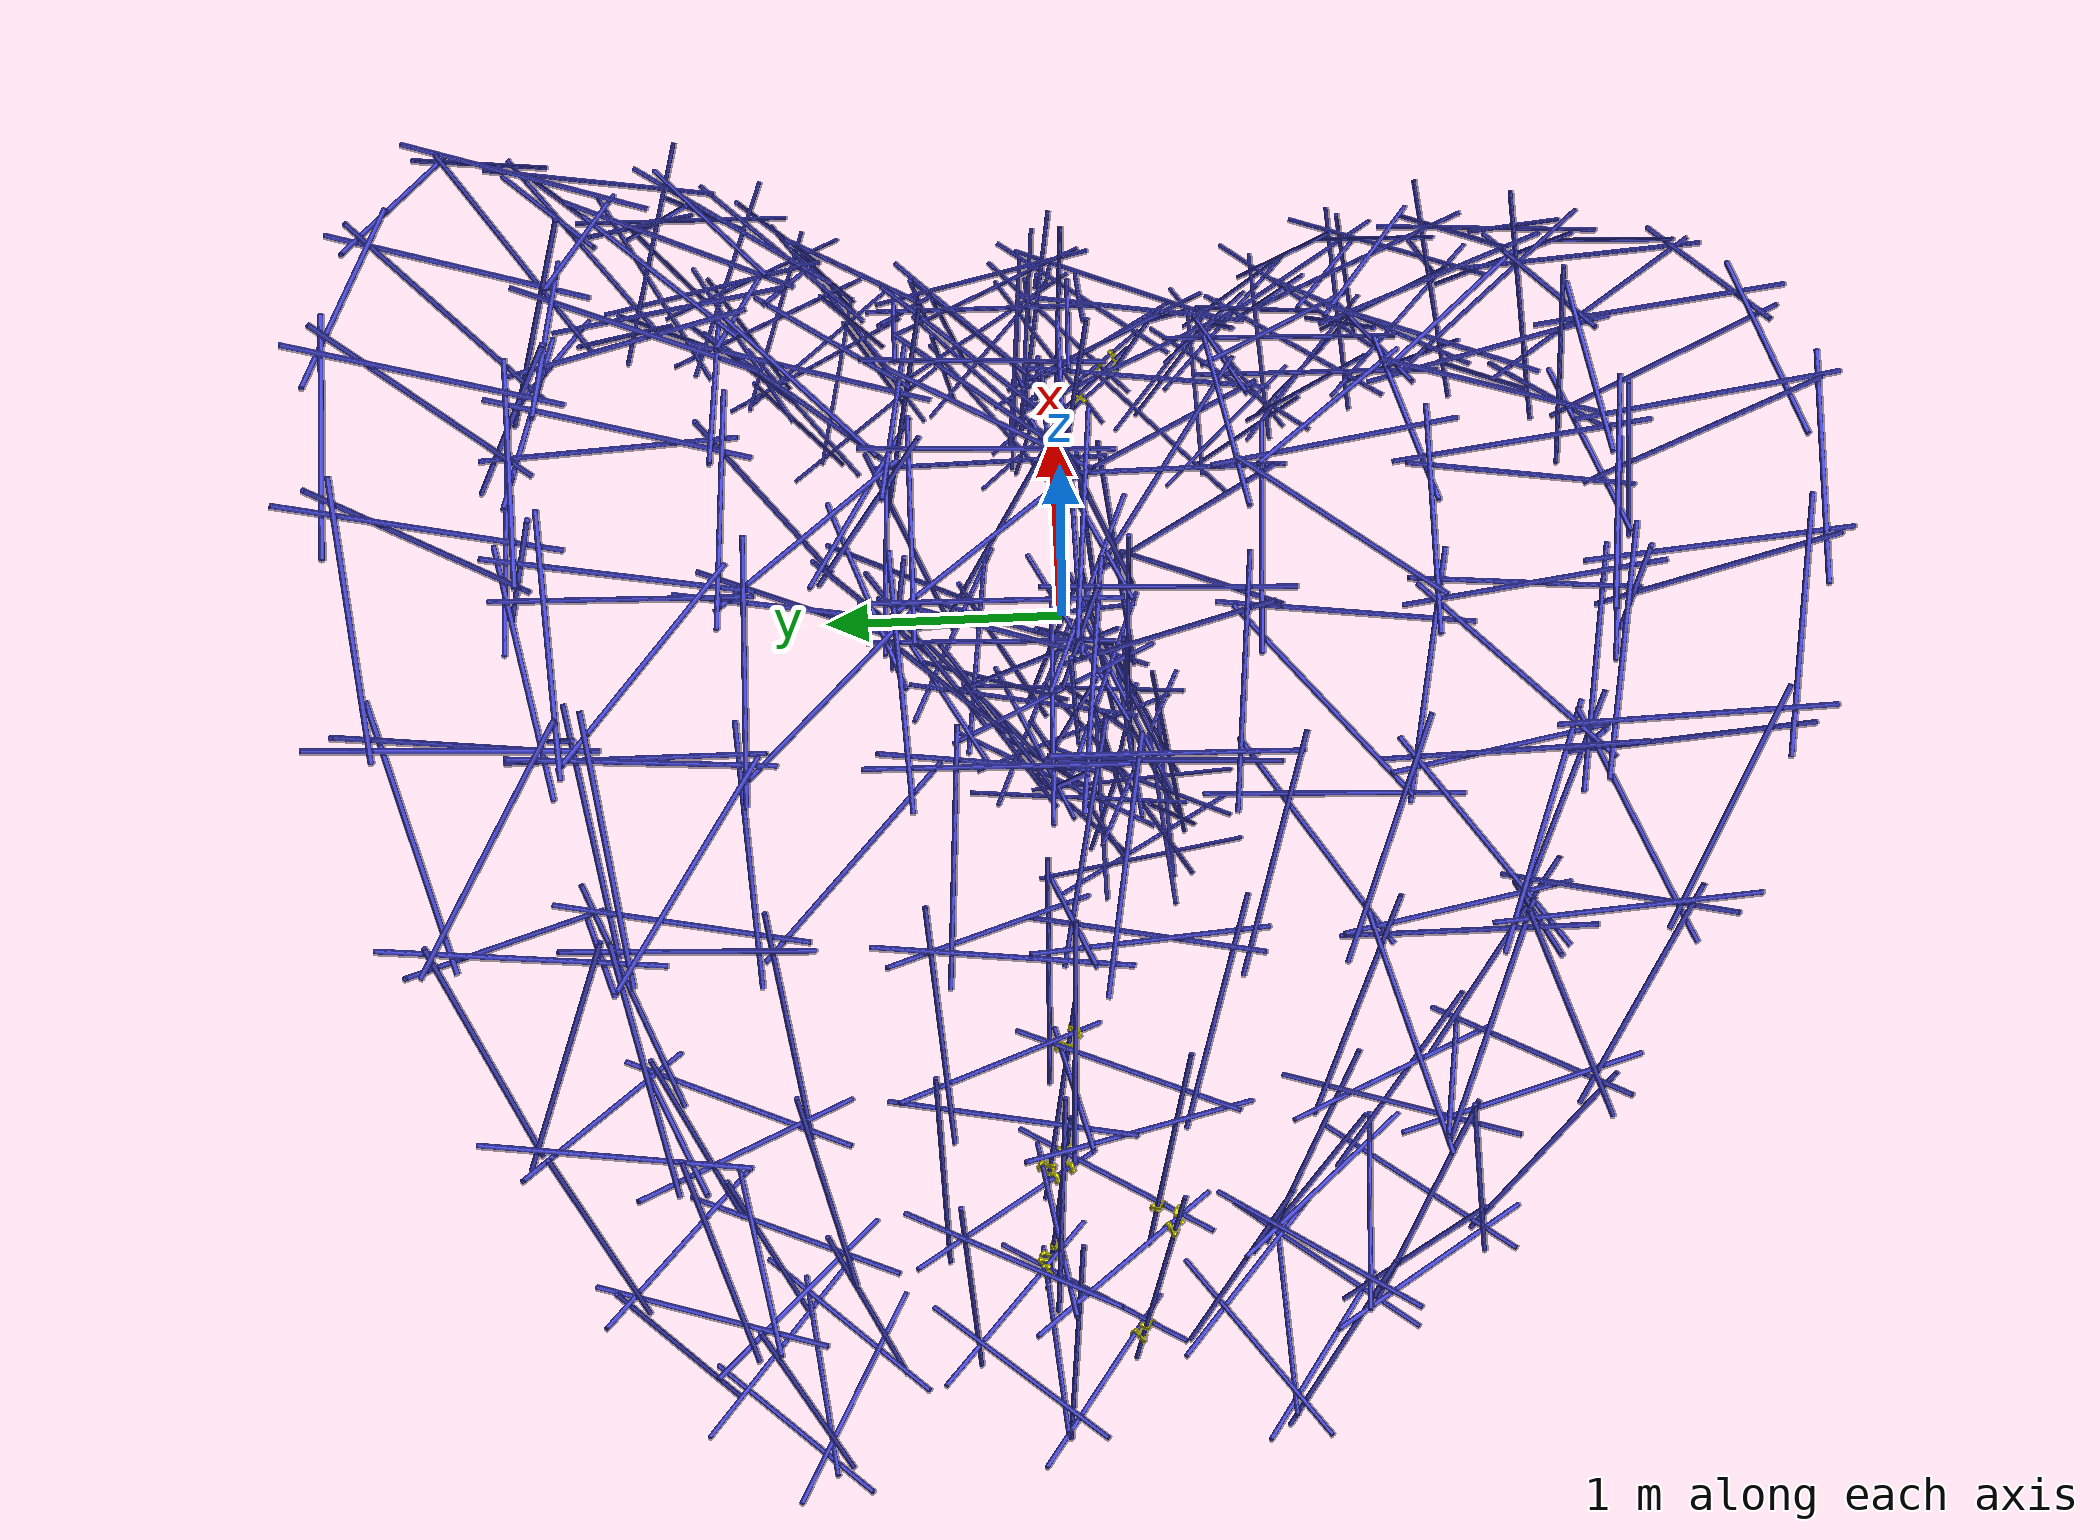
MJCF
<mujoco>
    <worldbody>
        <light diffuse=".5 .5 .5" pos="0 0 3" dir="0 0 -1"/>
        <body>
            <geom type="cylinder" size="0.01" rgba="0.3 .3 0.9 1"
                  fromto="-3.10402351196597 0.11722853041693071 -1.2772568552617027 -2.186906976394546 0.19171880572207556 -1.6688541727530575"/>
        </body>
        <body>
            <geom type="cylinder" size="0.01" rgba="0.3 .3 0.9 1"
                  fromto="3.1199078963211946 0.11722853571575698 -1.2772568831177735 2.202791360749764 0.1917188110209036 -1.6688542006091274"/>
        </body>
        <body>
            <geom type="cylinder" size="0.01" rgba="0.3 .3 0.9 1"
                  fromto="0.5079422233931297 -0.1803901135482615 -1.6326172291767966 -0.49205777660687033 -0.1803901135482615 -1.6326172291767966"/>
        </body>
        <body>
            <geom type="cylinder" size="0.01" rgba="0.3 .3 0.9 1"
                  fromto="-3.0521123034253037 -0.815224279846932 -1.3670463331611913 -2.0962399763883326 -0.8392962358772351 -1.659840860667762"/>
        </body>
        <body>
            <geom type="cylinder" size="0.01" rgba="0.3 .3 0.9 1"
                  fromto="3.0679967525879306 -0.8152242798577909 -1.3670463332932743 2.1121244255509524 -0.839296235888094 -1.6598408607998443"/>
        </body>
        <body>
            <geom type="cylinder" size="0.01" rgba="0.3 .3 0.9 1"
                  fromto="-3.207390086419089 1.044452415322981 -1.3576105851538252 -2.2713979291680815 1.2233369305560338 -1.6607920683853123"/>
        </body>
        <body>
            <geom type="cylinder" size="0.01" rgba="0.3 .3 0.9 1"
                  fromto="3.2232744986899746 1.0444524224560503 -1.3576105972432708 2.287282341438967 1.223336937689103 -1.6607920804747571"/>
        </body>
        <body>
            <geom type="cylinder" size="0.01" rgba="0.3 .3 0.9 1"
                  fromto="0.6141799636557792 -0.4922854460277044 -1.6326068155859959 -0.3857079710056226 -0.5072560047692996 -1.6326289405177163"/>
        </body>
        <body>
            <geom type="cylinder" size="0.01" rgba="0.3 .3 0.9 1"
                  fromto="-2.6953799338072315 -0.18864788189351067 -1.6624241696262723 -2.335246231835093 -0.3855236320546762 -0.750534014123802"/>
        </body>
        <body>
            <geom type="cylinder" size="0.01" rgba="0.3 .3 0.9 1"
                  fromto="-2.3167930373645547 0.17851952033199225 -1.8380282613364023 -1.88776005708975 0.05142845497598891 -0.9437248659815655"/>
        </body>
        <body>
            <geom type="cylinder" size="0.01" rgba="0.3 .3 0.9 1"
                  fromto="-2.140743240618285 0.37072515509989934 -1.7442878984683974 -2.7050965449061124 -0.39484313427517037 -1.4354019288246844"/>
        </body>
        <body>
            <geom type="cylinder" size="0.01" rgba="0.3 .3 0.9 1"
                  fromto="-2.088622895289973 0.0072645425742656755 -1.6440140518802229 -2.851437744510669 0.6113728417367437 -1.4134350660826749"/>
        </body>
        <body>
            <geom type="cylinder" size="0.01" rgba="0.3 .3 0.9 1"
                  fromto="-1.940542847859703 -0.04073183018669724 -1.207531498194526 -2.537471155291385 0.6922314434088115 -0.8812778616678166"/>
        </body>
        <body>
            <geom type="cylinder" size="0.01" rgba="0.3 .3 0.9 1"
                  fromto="-3.066958918649206 0.10691208943251418 -1.5040686922884683 -2.553923651781595 0.031960234877558946 -0.6489797878762747"/>
        </body>
        <body>
            <geom type="cylinder" size="0.01" rgba="0.3 .3 0.9 1"
                  fromto="-2.7162504197693735 0.1374045510837547 -0.9377408123441816 -2.1674045165633515 0.08032213452811199 -0.10376852728062058"/>
        </body>
        <body>
            <geom type="cylinder" size="0.01" rgba="0.3 .3 0.9 1"
                  fromto="-2.695671750393032 0.4705080277467264 -1.6673174137932016 -2.345845489315437 0.5097825340254083 -0.7313264414985777"/>
        </body>
        <body>
            <geom type="cylinder" size="0.01" rgba="0.3 .3 0.9 1"
                  fromto="-2.4457472214866556 0.5695549878924666 -1.0727383170191576 -2.035299552494763 0.5724599555152992 -0.1608587897885958"/>
        </body>
        <body>
            <geom type="cylinder" size="0.01" rgba="0.3 .3 0.9 1"
                  fromto="-2.8064117466618157 0.06829411816430841 -0.7359213143255666 -1.9102740346692784 0.19696697511421313 -1.1606335663611362"/>
        </body>
        <body>
            <geom type="cylinder" size="0.01" rgba="0.3 .3 0.9 1"
                  fromto="-3.2341672449680274 0.2100438374083815 -1.2845117690086763 -2.442771518324683 -0.30491417226671835 -1.613921926900195"/>
        </body>
        <body>
            <geom type="cylinder" size="0.01" rgba="0.3 .3 0.9 1"
                  fromto="-2.869061248168734 0.22376766080172672 -0.7591993804410142 -2.222516576678963 -0.5000852267190403 -1.0000665326142284"/>
        </body>
        <body>
            <geom type="cylinder" size="0.01" rgba="0.3 .3 0.9 1"
                  fromto="-3.1463214966352737 -0.04132275034822186 -1.2209226705861445 -2.490701326713271 0.6614155436403006 -1.4971853769971655"/>
        </body>
        <body>
            <geom type="cylinder" size="0.01" rgba="0.3 .3 0.9 1"
                  fromto="-2.784489435193642 -0.10911195214110059 -0.7080230650483821 -2.2953202227292735 0.7430597486534563 -0.893810238830372"/>
        </body>
        <body>
            <geom type="cylinder" size="0.01" rgba="0.3 .3 0.9 1"
                  fromto="-2.1220143907379025 0.17097579292785348 -1.255883856130622 -1.5986670271306878 0.017135692797245028 -0.4177664654285904"/>
        </body>
        <body>
            <geom type="cylinder" size="0.01" rgba="0.3 .3 0.9 1"
                  fromto="-1.8335840300268202 0.13447272857405146 -0.7212487579064458 -1.2248822428714874 0.10929598569427235 0.07175077925096618"/>
        </body>
        <body>
            <geom type="cylinder" size="0.01" rgba="0.3 .3 0.9 1"
                  fromto="-1.665920106939268 0.2641308972532652 -0.5570158235443023 -2.1311833347433122 -0.6034732416647905 -0.3815359472461417"/>
        </body>
        <body>
            <geom type="cylinder" size="0.01" rgba="0.3 .3 0.9 1"
                  fromto="-1.6398832094908968 -0.08004056915677715 -0.5690024450958564 -2.1194193747731305 0.715388534745383 -0.19841155630901053"/>
        </body>
        <body>
            <geom type="cylinder" size="0.01" rgba="0.3 .3 0.9 1"
                  fromto="-2.3203849885045287 0.05392040559499023 -0.35721898411434005 -1.6916246997083846 0.018046226572705493 0.4195522450853937"/>
        </body>
        <body>
            <geom type="cylinder" size="0.01" rgba="0.3 .3 0.9 1"
                  fromto="-2.200689705451481 0.5142853845216866 -0.4185428402097997 -1.5715853188391193 0.5774212886800232 0.35620971922526934"/>
        </body>
        <body>
            <geom type="cylinder" size="0.01" rgba="0.3 .3 0.9 1"
                  fromto="-2.38999093323212 -0.015563398612176371 -0.09082927125041529 -1.5998827003856206 0.10565000545811642 -0.6916922265587644"/>
        </body>
        <body>
            <geom type="cylinder" size="0.01" rgba="0.3 .3 0.9 1"
                  fromto="-2.3723963186915 0.2431152617718766 -0.21655546547467996 -2.0471990076679134 -0.663670583604901 -0.48485779406567264"/>
        </body>
        <body>
            <geom type="cylinder" size="0.01" rgba="0.3 .3 0.9 1"
                  fromto="-2.2712530340242267 -0.19127707601643706 -0.2493131156120767 -2.029982691883184 0.7706837890111764 -0.37745333630204314"/>
        </body>
        <body>
            <geom type="cylinder" size="0.01" rgba="0.3 .3 0.9 1"
                  fromto="-2.3987951835814982 -0.24569893838292955 -1.1004417921340237 -1.9539611880923644 -0.4164158157688256 -0.22124985391303298"/>
        </body>
        <body>
            <geom type="cylinder" size="0.01" rgba="0.3 .3 0.9 1"
                  fromto="-1.779725790226621 0.19292393242426442 0.33544281678991705 -1.5544658869911885 -0.7378170440266221 0.04738169350248578"/>
        </body>
        <body>
            <geom type="cylinder" size="0.01" rgba="0.3 .3 0.9 1"
                  fromto="-1.3780583114476457 0.19720156231541885 -0.126456852808444 -1.71366861601728 -0.7045841585623887 0.1458448862377244"/>
        </body>
        <body>
            <geom type="cylinder" size="0.01" rgba="0.3 .3 0.9 1"
                  fromto="-1.9106933006570372 -0.04662951590013442 0.4738358083646763 -1.158293189486507 0.10721001947107389 -0.16665421502939326"/>
        </body>
        <body>
            <geom type="cylinder" size="0.01" rgba="0.3 .3 0.9 1"
                  fromto="-1.8060613441921376 -0.19834506103204852 0.2600852800433364 -1.6754896237107246 0.7929904003036548 0.24576644947481463"/>
        </body>
        <body>
            <geom type="cylinder" size="0.01" rgba="0.3 .3 0.9 1"
                  fromto="-1.2813673971797357 -0.05007210066994183 -0.14290630626597456 -1.7681790410631635 0.729495499961546 0.25116066700783746"/>
        </body>
        <body>
            <geom type="cylinder" size="0.01" rgba="0.3 .3 0.9 1"
                  fromto="-2.151603289626358 -0.3935650471579617 -0.48525959075948655 -1.5071615300683447 -0.645701876555222 0.23662809981243482"/>
        </body>
        <body>
            <geom type="cylinder" size="0.01" rgba="0.3 .3 0.9 1"
                  fromto="-1.8504330711648151 0.2695502568172792 -1.1391042789175154 -2.4356236555791 -0.49676844510017304 -0.8739484247403613"/>
        </body>
        <body>
            <geom type="cylinder" size="0.01" rgba="0.3 .3 0.9 1"
                  fromto="2.2597377766749887 -0.4217251746929822 -0.8030903916691872 2.657863037395302 -0.13418977414457167 -1.6741929517663567"/>
        </body>
        <body>
            <geom type="cylinder" size="0.01" rgba="0.3 .3 0.9 1"
                  fromto="1.901653809747053 0.07853011659243947 -0.9390085210819121 2.3203791861710954 0.17231075987999844 -1.842266097902121"/>
        </body>
        <body>
            <geom type="cylinder" size="0.01" rgba="0.3 .3 0.9 1"
                  fromto="1.9241026205696201 0.2889262669726129 -1.2029898319655241 2.4531978907263223 -0.4961328982924549 -0.880902418161258"/>
        </body>
        <body>
            <geom type="cylinder" size="0.01" rgba="0.3 .3 0.9 1"
                  fromto="2.147717144317852 0.3596644552635073 -1.756356709906775 2.7064804467663492 -0.4105241142293927 -1.4487967332203884"/>
        </body>
        <body>
            <geom type="cylinder" size="0.01" rgba="0.3 .3 0.9 1"
                  fromto="2.121441475831844 -0.00366464533799693 -1.6781375532262939 2.8255202737483103 0.6158847473707514 -1.3311049952166396"/>
        </body>
        <body>
            <geom type="cylinder" size="0.01" rgba="0.3 .3 0.9 1"
                  fromto="2.594598103536896 0.08788045028281388 -0.6287906146538733 3.1119674488220497 0.061170795522343724 -1.4841358986776896"/>
        </body>
        <body>
            <geom type="cylinder" size="0.01" rgba="0.3 .3 0.9 1"
                  fromto="2.8130508146561652 0.27395488950167746 -0.7185760198320273 2.200386539373767 -0.4324240319300685 -1.0730775080512134"/>
        </body>
        <body>
            <geom type="cylinder" size="0.01" rgba="0.3 .3 0.9 1"
                  fromto="3.2181792595574166 0.24959717816226323 -1.264417424605187 2.476678150762737 -0.3153102607280225 -1.6264335722321703"/>
        </body>
        <body>
            <geom type="cylinder" size="0.01" rgba="0.3 .3 0.9 1"
                  fromto="3.1414729867164297 -0.04401568566779801 -1.1921905296346285 2.4903772063409875 0.6282269183916718 -1.5445598899153277"/>
        </body>
        <body>
            <geom type="cylinder" size="0.01" rgba="0.3 .3 0.9 1"
                  fromto="1.9502036502691595 -0.51693840014598 -0.24954551544474457 2.366258737814711 -0.33619373004576225 -1.140741076675736"/>
        </body>
        <body>
            <geom type="cylinder" size="0.01" rgba="0.3 .3 0.9 1"
                  fromto="2.336387016214424 0.5751751543023875 -0.7457156010104288 2.728422487490782 0.504534884928697 -1.6629495633144484"/>
        </body>
        <body>
            <geom type="cylinder" size="0.01" rgba="0.3 .3 0.9 1"
                  fromto="1.3473244750700033 0.05227696282365635 0.14203746728225553 1.857940322301765 0.05708408212653815 -0.7177580596657478"/>
        </body>
        <body>
            <geom type="cylinder" size="0.01" rgba="0.3 .3 0.9 1"
                  fromto="1.619196519457013 0.6134647565885025 0.3761668293060909 2.1689622436564377 0.5844893576677812 -0.4586493628900503"/>
        </body>
        <body>
            <geom type="cylinder" size="0.01" rgba="0.3 .3 0.9 1"
                  fromto="1.604073742495018 0.07596780794741242 -0.41566407847538667 2.140435511046462 0.16566197426836915 -1.2548726400167693"/>
        </body>
        <body>
            <geom type="cylinder" size="0.01" rgba="0.3 .3 0.9 1"
                  fromto="1.6848170647965688 0.2627775886320194 -0.5708637147005968 2.100719202084143 -0.6110235140285187 -0.31887751430689915"/>
        </body>
        <body>
            <geom type="cylinder" size="0.01" rgba="0.3 .3 0.9 1"
                  fromto="1.6917399927628765 -0.0921993275879398 -0.6027783049000721 2.274676245725395 0.6537708073009245 -0.280731906323866"/>
        </body>
        <body>
            <geom type="cylinder" size="0.01" rgba="0.3 .3 0.9 1"
                  fromto="1.6656921840060477 -0.015994450483542977 0.3841422496186091 2.305791295000887 -0.012960464761201607 -0.38414410522198805"/>
        </body>
        <body>
            <geom type="cylinder" size="0.01" rgba="0.3 .3 0.9 1"
                  fromto="2.14174311757062 0.03441137956442475 -0.14217524798378567 2.7978249204870096 0.033507003548388425 -0.8968644886557277"/>
        </body>
        <body>
            <geom type="cylinder" size="0.01" rgba="0.3 .3 0.9 1"
                  fromto="2.4395107157216103 0.049480509803510486 -0.12660123621807995 1.5583690953828935 0.1360061568481754 -0.5914697738826049"/>
        </body>
        <body>
            <geom type="cylinder" size="0.01" rgba="0.3 .3 0.9 1"
                  fromto="2.406656476398375 0.22048350469763456 -0.18582711194263557 1.9213615271244535 -0.6008641582577141 -0.4856217562693892"/>
        </body>
        <body>
            <geom type="cylinder" size="0.01" rgba="0.3 .3 0.9 1"
                  fromto="2.3059890620433663 -0.1699702142476145 -0.13765423590664505 1.969152874238965 0.747203217264806 -0.35057271587757954"/>
        </body>
        <body>
            <geom type="cylinder" size="0.01" rgba="0.3 .3 0.9 1"
                  fromto="1.5099585937682747 -0.6330695785581106 0.23652161125786386 2.165418553458025 -0.5223953006776032 -0.5105549882010809"/>
        </body>
        <body>
            <geom type="cylinder" size="0.01" rgba="0.3 .3 0.9 1"
                  fromto="2.028850538763635 0.5420064602492367 -0.167259884899567 2.4663133363153733 0.4257003022854011 -1.0589432246440635"/>
        </body>
        <body>
            <geom type="cylinder" size="0.01" rgba="0.3 .3 0.9 1"
                  fromto="1.3530761158239528 -0.05757262515486872 -0.1841923074330467 1.8234303899054112 0.6904513962145042 0.2840244375768848"/>
        </body>
        <body>
            <geom type="cylinder" size="0.01" rgba="0.3 .3 0.9 1"
                  fromto="1.9578526512608079 -0.021464244389992615 0.44356762149083595 1.200472634848019 0.13786627928468143 -0.1896695338973442"/>
        </body>
        <body>
            <geom type="cylinder" size="0.01" rgba="0.3 .3 0.9 1"
                  fromto="1.8491891404015632 0.1398026997101134 0.30879118121209403 1.6450733795177115 -0.8006869513119916 0.037100230904345555"/>
        </body>
        <body>
            <geom type="cylinder" size="0.01" rgba="0.3 .3 0.9 1"
                  fromto="1.3743461208748329 0.19591339099712357 -0.10584449778853244 1.6912313837044266 -0.7146590761799327 0.1595637014452267"/>
        </body>
        <body>
            <geom type="cylinder" size="0.01" rgba="0.3 .3 0.9 1"
                  fromto="1.7707622172097999 -0.19254959463598276 0.3736617305979282 1.652855368986664 0.7840795003178123 0.19395756806456754"/>
        </body>
        <body>
            <geom type="cylinder" size="0.01" rgba="0.3 .3 0.9 1"
                  fromto="2.785897017183892 -0.13721736103905435 -0.7892571262339659 2.303116139105626 0.708518759445024 -1.0165301740652417"/>
        </body>
        <body>
            <geom type="cylinder" size="0.01" rgba="0.3 .3 0.9 1"
                  fromto="1.8958085651933487 -0.0338784547149622 -1.1047663113348578 2.5362806849225734 0.6742712130173132 -0.8075803225328724"/>
        </body>
        <body>
            <geom type="cylinder" size="0.01" rgba="0.3 .3 0.9 1"
                  fromto="2.797499536325425 0.10699028724643611 -0.6813040113215216 1.9231940789005293 0.1967712010690139 -1.1583043830511774"/>
        </body>
        <body>
            <geom type="cylinder" size="0.01" rgba="0.3 .3 0.9 1"
                  fromto="-1.3453704175190495 0.599478582402913 0.6521297824743355 -0.42863003728741944 0.6607365918035715 1.0468886095283167"/>
        </body>
        <body>
            <geom type="cylinder" size="0.01" rgba="0.3 .3 0.9 1"
                  fromto="-0.9294854536297947 -0.08786011422288809 0.236741354785027 -1.153800815756746 0.7253307062217154 0.7737732978372915"/>
        </body>
        <body>
            <geom type="cylinder" size="0.01" rgba="0.3 .3 0.9 1"
                  fromto="-1.201647194963229 -0.21010069329883763 0.7086670739976992 -1.1625540917460597 0.7888366502758899 0.6842557468580535"/>
        </body>
        <body>
            <geom type="cylinder" size="0.01" rgba="0.3 .3 0.9 1"
                  fromto="-1.3554323521610456 -0.04068553957147891 0.9071272097055432 -0.8795620503889552 0.07127566328394686 0.0347671092043198"/>
        </body>
        <body>
            <geom type="cylinder" size="0.01" rgba="0.3 .3 0.9 1"
                  fromto="-1.183339962460984 0.09806839368774511 0.7578057302366354 -1.0873891318183624 -0.8802024621305709 0.5740135357465186"/>
        </body>
        <body>
            <geom type="cylinder" size="0.01" rgba="0.3 .3 0.9 1"
                  fromto="-0.8729758169194 0.10643478749385515 0.23845047948910092 -1.1423938973304715 -0.7882153586437131 0.5948421375896298"/>
        </body>
        <body>
            <geom type="cylinder" size="0.01" rgba="0.3 .3 0.9 1"
                  fromto="-1.2872997724342028 -0.6123335702405726 0.468499430708214 -0.4221650700412667 -0.7030427952038139 0.9617679004303827"/>
        </body>
        <body>
            <geom type="cylinder" size="0.01" rgba="0.3 .3 0.9 1"
                  fromto="-1.349661187561793 -0.030189062766499575 0.6123473826289154 -0.41176776672788407 -0.1387150844390863 0.941859193914008"/>
        </body>
        <body>
            <geom type="cylinder" size="0.01" rgba="0.3 .3 0.9 1"
                  fromto="-0.5930465121857438 -0.2145692043582006 0.917627797610618 -0.6428165248299607 0.7799970199905317 1.009066144195097"/>
        </body>
        <body>
            <geom type="cylinder" size="0.01" rgba="0.3 .3 0.9 1"
                  fromto="-0.782797252843217 0.5725756276558585 0.9335900158344739 0.20827816157616041 0.5860517910113803 1.0662094561691355"/>
        </body>
        <body>
            <geom type="cylinder" size="0.01" rgba="0.3 .3 0.9 1"
                  fromto="-0.5845336975512012 0.5920761755079127 1.2041909588689275 -0.39905899205175643 0.7073026823468691 0.22832109780056542"/>
        </body>
        <body>
            <geom type="cylinder" size="0.01" rgba="0.3 .3 0.9 1"
                  fromto="-0.643318267470427 0.6620934109267385 0.9192718754837483 -0.0002982171476517692 -0.023523437326515406 0.9118723975179734"/>
        </body>
        <body>
            <geom type="cylinder" size="0.01" rgba="0.3 .3 0.9 1"
                  fromto="0.25769319394716916 0.9548847206537978 0.49025910735236744 -0.6887383405670917 0.6321903163756577 0.5019069365304296"/>
        </body>
        <body>
            <geom type="cylinder" size="0.01" rgba="0.3 .3 0.9 1"
                  fromto="0.6997125453133108 0.6153369851888542 0.49285152755592154 -0.21576952821701667 1.0143285167273284 0.5447969874652432"/>
        </body>
        <body>
            <geom type="cylinder" size="0.01" rgba="0.3 .3 0.9 1"
                  fromto="-0.012810025312901985 -0.12583916064053824 0.9770931030984635 0.5781607137217151 0.6801495142959588 0.9433908557107236"/>
        </body>
        <body>
            <geom type="cylinder" size="0.01" rgba="0.3 .3 0.9 1"
                  fromto="-0.016893645661525625 0.5349618946434695 1.2042136158614043 -0.030501115160319614 1.0012796791734306 0.3197010039643726"/>
        </body>
        <body>
            <geom type="cylinder" size="0.01" rgba="0.3 .3 0.9 1"
                  fromto="-0.19241985003893092 0.686024596713958 1.056969148005761 0.7846963189425438 0.6079647691374408 0.8591039018565203"/>
        </body>
        <body>
            <geom type="cylinder" size="0.01" rgba="0.3 .3 0.9 1"
                  fromto="0.6814941216477521 0.5289311855349528 1.1724453614875658 0.4151946225405254 0.7226106710893028 0.2282140160797561"/>
        </body>
        <body>
            <geom type="cylinder" size="0.01" rgba="0.3 .3 0.9 1"
                  fromto="0.46888010753718845 0.6317936059387179 1.09399699515764 1.3334634521067628 0.6734343565557754 0.5932358862634537"/>
        </body>
        <body>
            <geom type="cylinder" size="0.01" rgba="0.3 .3 0.9 1"
                  fromto="0.8902942837503502 -0.03489436058989348 0.19275480373517606 1.1879708219297314 0.7145427610626687 0.784136811668001"/>
        </body>
        <body>
            <geom type="cylinder" size="0.01" rgba="0.3 .3 0.9 1"
                  fromto="1.144508010759644 -0.2106578587441028 0.669011361478205 1.1784108158920077 0.788355827672568 0.6403363870870473"/>
        </body>
        <body>
            <geom type="cylinder" size="0.01" rgba="0.3 .3 0.9 1"
                  fromto="1.2161234917161252 0.1445974327373989 0.6699125437812534 1.1497535147640008 -0.8446365006490737 0.5394853564463249"/>
        </body>
        <body>
            <geom type="cylinder" size="0.01" rgba="0.3 .3 0.9 1"
                  fromto="1.3923885289541218 -0.058012245817842256 0.8909712725256513 0.8800392053197683 -0.004654731786329691 0.03385334232713055"/>
        </body>
        <body>
            <geom type="cylinder" size="0.01" rgba="0.3 .3 0.9 1"
                  fromto="0.4539532027713946 -0.053353049463966684 1.0278406759167695 1.3604372009413908 -0.0830350605918273 0.6066450690104914"/>
        </body>
        <body>
            <geom type="cylinder" size="0.01" rgba="0.3 .3 0.9 1"
                  fromto="0.603248532352815 -0.21282802864994288 0.905528455214287 0.5681237026639963 0.7814448061810868 1.0064629699077172"/>
        </body>
        <body>
            <geom type="cylinder" size="0.01" rgba="0.3 .3 0.9 1"
                  fromto="0.5971433843728207 0.11193835485371473 0.8937664299698111 0.557460535775455 -0.879496522825228 0.7693391224809139"/>
        </body>
        <body>
            <geom type="cylinder" size="0.01" rgba="0.3 .3 0.9 1"
                  fromto="0.41428993382121604 -0.7672361838969941 0.9025581706165631 1.2977133307639903 -0.6234052165271535 0.4566032911057092"/>
        </body>
        <body>
            <geom type="cylinder" size="0.01" rgba="0.3 .3 0.9 1"
                  fromto="-0.2013442935382912 -0.7214607381327234 0.9508960524448917 0.787811654837995 -0.6257466279366035 0.839498929945389"/>
        </body>
        <body>
            <geom type="cylinder" size="0.01" rgba="0.3 .3 0.9 1"
                  fromto="-0.19181341229153048 -0.017198044998663065 1.027672170051963 0.8054748752118073 -0.022473765539672286 0.9542675490705519"/>
        </body>
        <body>
            <geom type="cylinder" size="0.01" rgba="0.3 .3 0.9 1"
                  fromto="-0.7916297077038124 -0.030797854255565582 0.9377680193951083 0.1907047012047869 -0.11947102263207654 1.1025593367763977"/>
        </body>
        <body>
            <geom type="cylinder" size="0.01" rgba="0.3 .3 0.9 1"
                  fromto="-0.7695331840385577 -0.7310695264327638 0.7683592879839778 0.2084220631228888 -0.8043845910031759 0.9638802225573251"/>
        </body>
        <body>
            <geom type="cylinder" size="0.01" rgba="0.3 .3 0.9 1"
                  fromto="-0.5590478975513022 0.10473049856277505 0.9604420214440377 -0.5138714035479097 -0.8867734998080721 0.8384629019022811"/>
        </body>
        <body>
            <geom type="cylinder" size="0.01" rgba="0.3 .3 0.9 1"
                  fromto="-1.1840095959012586 0.08043393911584396 0.2556996419855502 -0.20432630620965853 0.04793641317557018 0.4536000278032959"/>
        </body>
        <body>
            <geom type="cylinder" size="0.01" rgba="0.3 .3 0.9 1"
                  fromto="-0.4405832643629921 -0.07070875788178377 0.3485049421015758 -0.5859405791540269 0.7070996005852166 0.9599666404405727"/>
        </body>
        <body>
            <geom type="cylinder" size="0.01" rgba="0.3 .3 0.9 1"
                  fromto="-0.690425673660009 -0.11155965064007667 1.1328831474626821 -0.4726393439547323 0.013392223915408508 0.1649181978707177"/>
        </body>
        <body>
            <geom type="cylinder" size="0.01" rgba="0.3 .3 0.9 1"
                  fromto="-0.39761097141720114 -0.20303651427738245 0.3652548667585245 -0.39658951694136135 0.7957716765758089 0.4140519416230055"/>
        </body>
        <body>
            <geom type="cylinder" size="0.01" rgba="0.3 .3 0.9 1"
                  fromto="-0.46858743728884633 0.016599980352216548 0.3126708983543456 -0.6115665964987684 -0.7882414960823709 0.8886805838998382"/>
        </body>
        <body>
            <geom type="cylinder" size="0.01" rgba="0.3 .3 0.9 1"
                  fromto="-0.5859153718194321 -0.8198110985582421 0.8295133252949336 0.07295363999960358 -0.2516299063564933 0.3365003862225322"/>
        </body>
        <body>
            <geom type="cylinder" size="0.01" rgba="0.3 .3 0.9 1"
                  fromto="0.024597757002588594 -0.1631926597461799 0.2805809270540458 -0.05461969591078031 -0.8327430821240736 1.0191111072413563"/>
        </body>
        <body>
            <geom type="cylinder" size="0.01" rgba="0.3 .3 0.9 1"
                  fromto="0.6206161386914388 -0.728393305567181 0.8940881060832213 0.002609362669851123 -0.16864703024213235 0.34204487222273894"/>
        </body>
        <body>
            <geom type="cylinder" size="0.01" rgba="0.3 .3 0.9 1"
                  fromto="0.4039263328821221 0.03576008584642487 0.33913979917112425 0.5304641940780854 -0.8181056103182893 0.8440175493216908"/>
        </body>
        <body>
            <geom type="cylinder" size="0.01" rgba="0.3 .3 0.9 1"
                  fromto="0.21533172415404067 0.026287875815198092 0.4135871780386702 1.2046912155021445 0.0389408976493808 0.2686468526703223"/>
        </body>
        <body>
            <geom type="cylinder" size="0.01" rgba="0.3 .3 0.9 1"
                  fromto="-0.5045760654591191 -0.06342334952587514 0.41543309582778276 0.4332934778212163 -0.05933237170431127 0.3523142896952214"/>
        </body>
        <body>
            <geom type="cylinder" size="0.01" rgba="0.3 .3 0.9 1"
                  fromto="-0.685626844661293 0.07269938626004269 0.42795765105140626 0.25151621776794286 -0.2710086984646587 0.48818748614699325"/>
        </body>
        <body>
            <geom type="cylinder" size="0.01" rgba="0.3 .3 0.9 1"
                  fromto="-0.23871577355191675 -0.27903278403873166 0.4232426533016471 0.6860254459173802 0.0983434947541415 0.4726473212884641"/>
        </body>
        <body>
            <geom type="cylinder" size="0.01" rgba="0.3 .3 0.9 1"
                  fromto="-0.4917757051064626 0.7170662975598923 0.45460837417622013 0.5082045056530973 0.7120226269561698 0.45836862365088926"/>
        </body>
        <body>
            <geom type="cylinder" size="0.01" rgba="0.3 .3 0.9 1"
                  fromto="0.5015115151902663 0.7817385611241168 0.41464759350529823 0.5348957023150831 -0.21761058331729544 0.4009807155065963"/>
        </body>
        <body>
            <geom type="cylinder" size="0.01" rgba="0.3 .3 0.9 1"
                  fromto="0.03693720815078905 -0.21734397429273677 1.0295261306513015 0.01298643728302551 0.7783490872711507 1.1190900057817008"/>
        </body>
        <body>
            <geom type="cylinder" size="0.01" rgba="0.3 .3 0.9 1"
                  fromto="-0.018102004453233178 0.09830721075173798 0.9586599878393245 0.06878789944332908 -0.8937832520317048 0.8680693798549415"/>
        </body>
        <body>
            <geom type="cylinder" size="0.01" rgba="0.3 .3 0.9 1"
                  fromto="-0.04607297919625353 -0.005022804673950887 1.1839496873491329 -0.017238997128544042 -0.29423864432561686 0.227120131172746"/>
        </body>
        <body>
            <geom type="cylinder" size="0.01" rgba="0.3 .3 0.9 1"
                  fromto="0.6110537320189238 -0.1321927681352264 1.150695237776191 0.40922181353727183 0.010206054542509335 0.18168210474753543"/>
        </body>
        <body>
            <geom type="cylinder" size="0.01" rgba="0.3 .3 0.9 1"
                  fromto="0.9449682816788183 0.12545772591884585 0.2358463229974781 1.207446590766395 -0.7939530045060934 0.5287439946133627"/>
        </body>
        <body>
            <geom type="cylinder" size="0.01" rgba="0.3 .3 0.9 1"
                  fromto="0.48626873281060057 -0.11291658678445415 0.4069894428066392 0.6805147639872899 0.6450462290202701 1.0296939066010435"/>
        </body>
        <body>
            <geom type="cylinder" size="0.01" rgba="0.3 .3 0.9 1"
                  fromto="0.21839339451392448 -0.5708962228674359 -0.9329854291751757 0.251706354360266 0.4264627717149665 -0.8684464283163551"/>
        </body>
        <body>
            <geom type="cylinder" size="0.01" rgba="0.3 .3 0.9 1"
                  fromto="-0.35008088018653893 -0.4786239874858378 -0.9097395331241338 0.58548626955222 -0.12947675379693635 -0.8567271049861771"/>
        </body>
        <body>
            <geom type="cylinder" size="0.01" rgba="0.3 .3 0.9 1"
                  fromto="-0.5818649143154175 -0.14836214358223465 -0.9624366063448216 0.33633126458197893 -0.5437394783492309 -0.9380944574919949"/>
        </body>
        <body>
            <geom type="cylinder" size="0.01" rgba="0.3 .3 0.9 1"
                  fromto="-0.27954651402076536 0.4377617595571355 -0.9561437958166858 -0.3046362561652245 -0.5542095779330687 -1.0800928596978614"/>
        </body>
        <body>
            <geom type="cylinder" size="0.01" rgba="0.3 .3 0.9 1"
                  fromto="0.3790995845819083 0.30633800393100863 -0.9173910976391468 -0.5521022837437997 -0.02504191703429548 -0.7655674222530777"/>
        </body>
        <body>
            <geom type="cylinder" size="0.01" rgba="0.3 .3 0.9 1"
                  fromto="0.558929207325292 -0.059485960173280006 -0.8030453672241533 -0.3564925949796631 0.3146545846532618 -0.9514427276509795"/>
        </body>
        <body>
            <geom type="cylinder" size="0.01" rgba="0.3 .3 0.9 1"
                  fromto="0.23917550618497785 -0.5079675723718289 -0.9890493140040976 -0.16887471324779568 0.4041308540153743 -0.9494074295527657"/>
        </body>
        <body>
            <geom type="cylinder" size="0.01" rgba="0.3 .3 0.9 1"
                  fromto="-0.4852026519087076 -0.33280027552033076 -0.8921100978338807 0.5089670104415731 -0.26209249020663705 -0.9735170481413433"/>
        </body>
        <body>
            <geom type="cylinder" size="0.01" rgba="0.3 .3 0.9 1"
                  fromto="0.03802675370322106 0.4818371891858071 -0.9461876551046172 -0.40459763746724065 -0.3996301756442193 -1.1108051908673258"/>
        </body>
        <body>
            <geom type="cylinder" size="0.01" rgba="0.3 .3 0.9 1"
                  fromto="0.35680797450876867 -0.04207449558774634 -0.175314530908673 -0.08924512941715079 -0.44534013685525586 -0.9743223225172121"/>
        </body>
        <body>
            <geom type="cylinder" size="0.01" rgba="0.3 .3 0.9 1"
                  fromto="-0.2517326716056658 -0.13645041232097554 -0.10885350003437999 -0.15140012082933652 0.13828665406344598 -1.0651238193527184"/>
        </body>
        <body>
            <geom type="cylinder" size="0.01" rgba="0.3 .3 0.9 1"
                  fromto="-0.0873325807902745 0.5999136689942333 -0.181649349778932 0.18376159678459913 -0.021395009147742172 -0.9168251609632194"/>
        </body>
        <body>
            <geom type="cylinder" size="0.01" rgba="0.3 .3 0.9 1"
                  fromto="0.29261576514299037 -0.0914992551150533 -0.10019240297904153 0.27382246107137576 0.1605843863213927 -1.0677153481551303"/>
        </body>
        <body>
            <geom type="cylinder" size="0.01" rgba="0.3 .3 0.9 1"
                  fromto="-0.2379808382562132 0.014809573220311734 -0.16725043160719744 0.0006593570266133497 -0.39288648161601536 -1.0486327459670162"/>
        </body>
        <body>
            <geom type="cylinder" size="0.01" rgba="0.3 .3 0.9 1"
                  fromto="-0.040140397288425333 0.5359451719729549 -0.09923753751082476 -0.32078780928409856 0.04538632175236579 -0.9242157460778064"/>
        </body>
        <body>
            <geom type="cylinder" size="0.01" rgba="0.3 .3 0.9 1"
                  fromto="0.2995994679290561 -0.2631693676190494 -1.7897249082310747 0.17537503779444563 -0.3414908119665636 -0.8005666588528215"/>
        </body>
        <body>
            <geom type="cylinder" size="0.01" rgba="0.3 .3 0.9 1"
                  fromto="-0.028575761934590105 -0.635938577687515 -1.7459183031262142 -0.4303146280709882 -0.3666027277757866 -0.8706674342961602"/>
        </body>
        <body>
            <geom type="cylinder" size="0.01" rgba="0.3 .3 0.9 1"
                  fromto="-0.2871733825439975 -0.2912938896458943 -1.6423291354109069 -0.0038417450927852315 0.15267990504677975 -0.7922641656318885"/>
        </body>
        <body>
            <geom type="cylinder" size="0.01" rgba="0.3 .3 0.9 1"
                  fromto="-0.08643517886095253 -0.5821303096257218 -1.716752341542357 0.23303559814937813 -0.41930747959680836 -0.7832497177336233"/>
        </body>
        <body>
            <geom type="cylinder" size="0.01" rgba="0.3 .3 0.9 1"
                  fromto="-0.13084848833408813 -0.1218836010529234 -1.7754263294100976 -0.193609123429205 -0.27436454309303926 -0.7891146824155906"/>
        </body>
        <body>
            <geom type="cylinder" size="0.01" rgba="0.3 .3 0.9 1"
                  fromto="0.14492784917575108 -0.19333682198609559 -1.7370919937723026 -0.062106275927583 0.2517509258639894 -0.8658665535121847"/>
        </body>
        <body>
            <geom type="cylinder" size="0.01" rgba="0.3 .3 0.9 1"
                  fromto="-0.20814084246350006 -0.19940968321032493 -0.8185691233474165 -0.3144149643692984 -0.603934357301048 -1.7269003399556244"/>
        </body>
        <body>
            <geom type="cylinder" size="0.01" rgba="0.3 .3 0.9 1"
                  fromto="-0.38234024729578664 -0.11088037271900397 -0.1128690437615738 -0.2541981363695669 -0.2638882887714331 -1.0927507595990855"/>
        </body>
        <body>
            <geom type="cylinder" size="0.01" rgba="0.3 .3 0.9 1"
                  fromto="-0.19689741333431243 0.1948595943681326 -0.870108628219127 -0.1791019382157728 -0.29295165417002345 -1.7428763561198275"/>
        </body>
        <body>
            <geom type="cylinder" size="0.01" rgba="0.3 .3 0.9 1"
                  fromto="-0.2534148012190869 0.4312221643918388 -0.10714731119242016 -0.327213344379345 0.04917444989426656 -1.028338561082803"/>
        </body>
        <body>
            <geom type="cylinder" size="0.01" rgba="0.3 .3 0.9 1"
                  fromto="-0.03173583684048964 -0.2592971024469204 -0.10607659041504669 0.011853678798225076 -0.3219726735662398 -1.103158195355811"/>
        </body>
        <body>
            <geom type="cylinder" size="0.01" rgba="0.3 .3 0.9 1"
                  fromto="-0.05836176191743192 0.5751650615831227 -0.09517674691001776 -0.0927032077579284 0.11086935371654505 -0.9801909619112554"/>
        </body>
        <body>
            <geom type="cylinder" size="0.01" rgba="0.3 .3 0.9 1"
                  fromto="0.33341751696247 -0.2627414874776015 -0.8051878713312085 0.28100258346089646 -0.5749404085735019 -1.7537575885436976"/>
        </body>
        <body>
            <geom type="cylinder" size="0.01" rgba="0.3 .3 0.9 1"
                  fromto="0.18676419872211625 0.0819772933738463 -0.7840092587292944 0.2469404944819189 -0.3127632535275371 -1.7008291505622688"/>
        </body>
        <body>
            <geom type="cylinder" size="0.01" rgba="0.3 .3 0.9 1"
                  fromto="0.3570736418520326 -0.09431428572512246 -0.11012547026454755 0.15903639427151717 -0.2512142113726288 -1.0776809786993555"/>
        </body>
        <body>
            <geom type="cylinder" size="0.01" rgba="0.3 .3 0.9 1"
                  fromto="0.26372256389615245 0.4426978601202425 -0.09360309461887151 0.16491404245741137 0.07667433062905005 -1.0189482474942184"/>
        </body>
        <body>
            <geom type="cylinder" size="0.01" rgba="0.3 .3 0.9 1"
                  fromto="-0.42625922655410875 0.04600533757410297 -1.701460160908486 0.10914161579120929 -0.7984880236054774 -1.7147605721629198"/>
        </body>
        <body>
            <geom type="cylinder" size="0.01" rgba="0.3 .3 0.9 1"
                  fromto="-0.07345649256147624 -0.8049894216487292 -1.5966189795885237 0.3782498825478342 0.08717723916673847 -1.5966151081691524"/>
        </body>
        <body>
            <geom type="cylinder" size="0.01" rgba="0.3 .3 0.9 1"
                  fromto="-0.20721099048263625 -0.8468685394623101 -1.5899149802982175 -0.3838160567089446 0.13736353139394808 -1.5998084772129348"/>
        </body>
        <body>
            <geom type="cylinder" size="0.01" rgba="0.3 .3 0.9 1"
                  fromto="0.15701140782576317 0.1571012916010428 -1.6686191710823475 0.23402480436930517 -0.8399287664936619 -1.6686162562916378"/>
        </body>
        <body>
            <geom type="cylinder" size="0.01" rgba="0.3 .3 0.9 1"
                  fromto="0.0699030772959901 -0.26240940690985504 -0.8240676381298959 0.0017751618050709794 -0.5856943738087317 -1.7679137152569109"/>
        </body>
        <body>
            <geom type="cylinder" size="0.01" rgba="0.3 .3 0.9 1"
                  fromto="0.403024588551844 -0.43967685064163753 -1.5780532114853623 -0.5935932769857359 -0.49776898997078156 -1.5199314991956947"/>
        </body>
        <body>
            <geom type="cylinder" size="0.01" rgba="0.3 .3 0.9 1"
                  fromto="-0.6211142240070586 -0.007241165113653025 -0.2936451798287174 0.3210985674338289 -0.3422178368916846 -0.28857714177736016"/>
        </body>
        <body>
            <geom type="cylinder" size="0.01" rgba="0.3 .3 0.9 1"
                  fromto="-0.47199851347721733 0.48389120401895624 -0.2407303723950056 0.002454874874466384 -0.3963219880733675 -0.2298345590591251"/>
        </body>
        <body>
            <geom type="cylinder" size="0.01" rgba="0.3 .3 0.9 1"
                  fromto="-0.20285021957006677 0.6652891974778861 -0.17648251196525222 -0.2863058287232647 -0.3135877941910792 -0.36312386987390655"/>
        </body>
        <body>
            <geom type="cylinder" size="0.01" rgba="0.3 .3 0.9 1"
                  fromto="0.2757396417070268 0.7500049369073096 -0.32625876484552707 -0.6207361260689694 0.33466134483679966 -0.17191856166954733"/>
        </body>
        <body>
            <geom type="cylinder" size="0.01" rgba="0.3 .3 0.9 1"
                  fromto="0.5035040718255459 0.32514260633513636 -0.2054308442360282 -0.48749281624106544 0.42116146856641024 -0.29873435937938075"/>
        </body>
        <body>
            <geom type="cylinder" size="0.01" rgba="0.3 .3 0.9 1"
                  fromto="0.617928727909387 0.29772211379787983 -0.3137585946806398 -0.31754081215996877 0.6504499163356741 -0.29185341448764257"/>
        </body>
        <body>
            <geom type="cylinder" size="0.01" rgba="0.3 .3 0.9 1"
                  fromto="-0.023060130081205443 -0.3741370186756594 -0.35677952495875687 0.3628903147527325 0.5483293884056852 -0.36667810763117825"/>
        </body>
        <body>
            <geom type="cylinder" size="0.01" rgba="0.3 .3 0.9 1"
                  fromto="-0.3346185763278413 -0.27279146057617254 -0.3296978242349593 0.5776127667809305 0.13670724246083132 -0.3176649999206864"/>
        </body>
        <body>
            <geom type="cylinder" size="0.01" rgba="0.3 .3 0.9 1"
                  fromto="0.2648025294837879 -0.33354407591797575 -0.2984690837219617 0.15078149369355742 0.6591798220541669 -0.259759061863045"/>
        </body>
        <body>
            <geom type="cylinder" size="0.01" rgba="0.3 .3 0.9 1"
                  fromto="-1.5958166053900058 0.05931439130996097 -0.14547215351377107 -0.8260939166786656 -0.13975406836746274 0.4610744076376756"/>
        </body>
        <body>
            <geom type="cylinder" size="0.01" rgba="0.3 .3 0.9 1"
                  fromto="-1.9226987906938646 -0.09095481817585593 0.23026998844937752 -1.057165369913676 -0.26000801007126917 0.701728274857111"/>
        </body>
        <body>
            <geom type="cylinder" size="0.01" rgba="0.3 .3 0.9 1"
                  fromto="0.2925369769598518 0.49745148997057775 -0.3728967592472874 0.5956834039875645 0.020290697931301338 0.4519788812711991"/>
        </body>
        <body>
            <geom type="cylinder" size="0.01" rgba="0.3 .3 0.9 1"
                  fromto="0.07098490379250677 -0.2224254329269133 -0.3286174948058298 -0.4082545325556737 0.11750013540559223 0.48056738557843914"/>
        </body>
        <body>
            <geom type="cylinder" size="0.01" rgba="0.3 .3 0.9 1"
                  fromto="-0.36843668371938065 0.34478191296519967 -0.268152899729067 -0.12848921695487547 0.794072172866775 0.5218872736487628"/>
        </body>
        <body>
            <geom type="cylinder" size="0.01" rgba="0.3 .3 0.9 1"
                  fromto="-0.037314938602577286 -0.3118852291536989 -0.3323457673896699 0.6012491765528907 -0.17802116353276176 0.4254908131282873"/>
        </body>
        <body>
            <geom type="cylinder" size="0.01" rgba="0.3 .3 0.9 1"
                  fromto="-0.16950414690769122 0.46701254147677673 -0.2907788340385038 -0.37416890058685226 -0.21096879238019284 0.4152336655271718"/>
        </body>
        <body>
            <geom type="cylinder" size="0.01" rgba="0.3 .3 0.9 1"
                  fromto="0.27214252173286724 0.42435965887898597 -0.22019948654889365 0.01920747579376325 0.9482462978558939 0.5181545288375338"/>
        </body>
        <body>
            <geom type="cylinder" size="0.01" rgba="0.3 .3 0.9 1"
                  fromto="-0.5944866313816277 -0.013413612905122108 0.5398260546893838 -0.37111046530865366 -0.051940953749765484 -0.4341445467344889"/>
        </body>
        <body>
            <geom type="cylinder" size="0.01" rgba="0.3 .3 0.9 1"
                  fromto="-0.5127550580166869 0.7067606937277997 0.6040675874455821 -0.39769518992554964 0.25796983860261236 -0.2821310331304452"/>
        </body>
        <body>
            <geom type="cylinder" size="0.01" rgba="0.3 .3 0.9 1"
                  fromto="-0.034104772574799824 -0.27140430262884685 0.579720169813243 -0.11760206179101118 -0.2801078667776231 -0.4167498250509536"/>
        </body>
        <body>
            <geom type="cylinder" size="0.01" rgba="0.3 .3 0.9 1"
                  fromto="0.4011815007931716 -0.08045979437212303 0.5854489238302709 0.31838341096427314 -0.1712868321965857 -0.4069698010639744"/>
        </body>
        <body>
            <geom type="cylinder" size="0.01" rgba="0.3 .3 0.9 1"
                  fromto="0.45161850992443675 0.7943770700940789 0.569480180819312 0.19915793908097612 0.4787836275699231 -0.3452134505158708"/>
        </body>
        <body>
            <geom type="cylinder" size="0.01" rgba="0.3 .3 0.9 1"
                  fromto="-0.08146848039071841 1.0038314247914961 0.5507812381117105 0.03712123729000183 0.5627277614392501 -0.3388052034652931"/>
        </body>
        <body>
            <geom type="cylinder" size="0.01" rgba="0.3 .3 0.9 1"
                  fromto="1.029242645363233 -0.1362793049372133 0.7042889163337502 1.8528147151644063 -0.1406268527025496 0.13709393692028193"/>
        </body>
        <body>
            <geom type="cylinder" size="0.01" rgba="0.3 .3 0.9 1"
                  fromto="0.8427106980632431 0.12478994228354523 0.49861262436437714 1.5589075243451376 0.1507894403304455 -0.19880126431654777"/>
        </body>
        <body>
            <geom type="cylinder" size="0.01" rgba="0.3 .3 0.9 1"
                  fromto="1.0210040464291765 0.7254800695923258 0.7222860914760001 1.7822622740578495 0.5370108923393229 0.10183038790544652"/>
        </body>
        <body>
            <geom type="cylinder" size="0.01" rgba="0.3 .3 0.9 1"
                  fromto="0.9944375236599683 -0.7693484521181162 0.6600153321216604 1.698193343964455 -0.7593480301673488 -0.05035621639950638"/>
        </body>
        <body>
            <geom type="cylinder" size="0.01" rgba="0.3 .3 0.9 1"
                  fromto="-1.7208876855041453 -0.6260645914806702 -0.03560830147201011 -1.05631874949637 -0.881145248430176 0.666732063126025"/>
        </body>
        <body>
            <geom type="cylinder" size="0.01" rgba="0.3 .3 0.9 1"
                  fromto="-1.8149706484009442 0.49606718276654505 0.1400519343523734 -0.986800490107484 0.4299040409091912 0.6966097728307781"/>
        </body>
        <body>
            <geom type="cylinder" size="0.01" rgba="0.3 .3 0.9 1"
                  fromto="-2.7196271203336053 0.7855586238585666 -1.6574870454557031 -2.439497985484671 1.0366289511024807 -0.730938957882036"/>
        </body>
        <body>
            <geom type="cylinder" size="0.01" rgba="0.3 .3 0.9 1"
                  fromto="-2.5575553747876683 0.940869793228563 -0.9851215888845317 -2.120930364534779 1.0941118765182498 -0.09862541611744202"/>
        </body>
        <body>
            <geom type="cylinder" size="0.01" rgba="0.3 .3 0.9 1"
                  fromto="-2.172316272543668 1.0639708088954762 -0.38085221704311945 -1.6171191871272441 1.1633645101872911 0.4449062757915727"/>
        </body>
        <body>
            <geom type="cylinder" size="0.01" rgba="0.3 .3 0.9 1"
                  fromto="-2.4203971574946834 1.2026411905217884 -1.7632726867273294 -2.1495631635562447 1.4570632774647798 -0.8348771086449437"/>
        </body>
        <body>
            <geom type="cylinder" size="0.01" rgba="0.3 .3 0.9 1"
                  fromto="-2.202933643340458 1.4231393298177988 -1.1007963548573623 -1.9022200527192794 1.6694943131088937 -0.179449211472545"/>
        </body>
        <body>
            <geom type="cylinder" size="0.01" rgba="0.3 .3 0.9 1"
                  fromto="-2.008864268900126 1.5641062744601495 -0.38917201159761206 -1.4160900619525592 1.8667374812419109 0.3571744845149458"/>
        </body>
        <body>
            <geom type="cylinder" size="0.01" rgba="0.3 .3 0.9 1"
                  fromto="-2.1923846558660998 1.3849494272013185 -1.6450686676801662 -2.8639049738345577 0.6774833053309575 -1.4247231459166065"/>
        </body>
        <body>
            <geom type="cylinder" size="0.01" rgba="0.3 .3 0.9 1"
                  fromto="-2.1266123154881953 1.6343140383557557 -1.0455471977492565 -2.5644233891079153 0.7590469770911277 -0.8400501532908888"/>
        </body>
        <body>
            <geom type="cylinder" size="0.01" rgba="0.3 .3 0.9 1"
                  fromto="-1.8182390243143942 1.8014240044621666 -0.3636673726572617 -2.2466419479281043 0.9012116478844074 -0.2856375828078628"/>
        </body>
        <body>
            <geom type="cylinder" size="0.01" rgba="0.3 .3 0.9 1"
                  fromto="-2.174647419060733 1.0275836494923603 -1.72183189361256 -2.9796927998296567 1.5939625843485405 -1.5454322420998732"/>
        </body>
        <body>
            <geom type="cylinder" size="0.01" rgba="0.3 .3 0.9 1"
                  fromto="-1.9961431357903123 1.3916212657941482 -1.0709335409942442 -2.783957985641017 1.870918979248902 -0.6841242026481258"/>
        </body>
        <body>
            <geom type="cylinder" size="0.01" rgba="0.3 .3 0.9 1"
                  fromto="-1.7802010423543493 1.589679162070187 -0.38679700584523347 -2.502211285530514 2.0364260890972474 0.14151955829086904"/>
        </body>
        <body>
            <geom type="cylinder" size="0.01" rgba="0.3 .3 0.9 1"
                  fromto="-3.142323650490617 0.9950833046804011 -1.4889419767380299 -2.8633380682866374 1.266696426272949 -0.567859267584798"/>
        </body>
        <body>
            <geom type="cylinder" size="0.01" rgba="0.3 .3 0.9 1"
                  fromto="-2.916451051071597 1.29026019878755 -0.7526768367513008 -2.4347951026138404 1.4810664912085532 0.10265965030382684"/>
        </body>
        <body>
            <geom type="cylinder" size="0.01" rgba="0.3 .3 0.9 1"
                  fromto="-2.530248556908184 1.4970215887075486 -0.0048249821136596704 -1.8575548592047824 1.665155639619421 0.7157401641389809"/>
        </body>
        <body>
            <geom type="cylinder" size="0.01" rgba="0.3 .3 0.9 1"
                  fromto="-2.7904512412913576 1.4840108973569706 -1.6320047260407893 -2.6377438860133395 1.8481856529203675 -0.7132788631990311"/>
        </body>
        <body>
            <geom type="cylinder" size="0.01" rgba="0.3 .3 0.9 1"
                  fromto="-2.6866947153705354 1.7309805634050583 -0.8140362824251278 -2.4155808546209556 1.9575833880450197 0.12145740241440572"/>
        </body>
        <body>
            <geom type="cylinder" size="0.01" rgba="0.3 .3 0.9 1"
                  fromto="-2.343128030597647 2.0088727470226573 -0.016065034872426054 -1.9203218735161087 2.2723082775273493 0.851020125190677"/>
        </body>
        <body>
            <geom type="cylinder" size="0.01" rgba="0.3 .3 0.9 1"
                  fromto="-2.943777431592629 1.1905059685209736 -0.6206381701909778 -2.043174348412016 1.4277343180389863 -0.9848315209684548"/>
        </body>
        <body>
            <geom type="cylinder" size="0.01" rgba="0.3 .3 0.9 1"
                  fromto="-2.572849576500886 1.3790617580658608 0.10448423550283636 -1.8134382039104082 1.7395153807174228 -0.4371499150984821"/>
        </body>
        <body>
            <geom type="cylinder" size="0.01" rgba="0.3 .3 0.9 1"
                  fromto="-3.319873875336434 1.1829302939010518 -1.3137457079213948 -2.42324856185364 0.7784096779182619 -1.4938182446025443"/>
        </body>
        <body>
            <geom type="cylinder" size="0.01" rgba="0.3 .3 0.9 1"
                  fromto="-3.007081028402652 1.4305403752842754 -0.6563209043847518 -2.2693775410304156 0.8640761545085613 -1.0236243910273513"/>
        </body>
        <body>
            <geom type="cylinder" size="0.01" rgba="0.3 .3 0.9 1"
                  fromto="-2.567879454433111 1.6349440890278988 0.06369076157589948 -2.022953059168607 0.9074645159683161 -0.35323692343084456"/>
        </body>
        <body>
            <geom type="cylinder" size="0.01" rgba="0.3 .3 0.9 1"
                  fromto="-3.274400937039047 0.9042417814269061 -1.366149041577304 -2.6326065740428604 1.5938210540621203 -1.7016791033872822"/>
        </body>
        <body>
            <geom type="cylinder" size="0.01" rgba="0.3 .3 0.9 1"
                  fromto="-2.894932428238164 1.0206679361640134 -0.6741478689122791 -2.5652547560708 1.9517201664152672 -0.8305268221587783"/>
        </body>
        <body>
            <geom type="cylinder" size="0.01" rgba="0.3 .3 0.9 1"
                  fromto="-2.4476620032875545 1.230758322095598 0.034331046830869516 -2.3417861079543343 2.2224024207067465 0.10803502553670397"/>
        </body>
        <body>
            <geom type="cylinder" size="0.01" rgba="0.3 .3 0.9 1"
                  fromto="-1.87485048574775 1.6879355506261717 0.7551382603742165 -2.3961902266658086 2.0470718817706945 -0.018958613532109148"/>
        </body>
        <body>
            <geom type="cylinder" size="0.01" rgba="0.3 .3 0.9 1"
                  fromto="-1.4707814801183616 1.9790496908153141 0.30459872694099355 -1.6869651108041381 1.0029673181902812 0.32757348861988844"/>
        </body>
        <body>
            <geom type="cylinder" size="0.01" rgba="0.3 .3 0.9 1"
                  fromto="-1.9072637572684457 1.8342434249434643 0.7540203713958884 -1.688488238052976 0.9926274416765875 0.26023923678083594"/>
        </body>
        <body>
            <geom type="cylinder" size="0.01" rgba="0.3 .3 0.9 1"
                  fromto="-2.09415998778141 1.6208413825316725 0.772329777700564 -1.407847111821134 1.8976400949700647 0.09975479371470342"/>
        </body>
        <body>
            <geom type="cylinder" size="0.01" rgba="0.3 .3 0.9 1"
                  fromto="-1.8887527719434658 1.4811046019490792 0.5780602230549232 -1.917253175073391 2.446770669318738 0.8362786835728553"/>
        </body>
        <body>
            <geom type="cylinder" size="0.01" rgba="0.3 .3 0.9 1"
                  fromto="-1.4379412106668354 1.8145554636491088 0.1900031550895096 -2.0184128148235416 2.334356509764019 0.8167882771413892"/>
        </body>
        <body>
            <geom type="cylinder" size="0.01" rgba="0.3 .3 0.9 1"
                  fromto="1.7119667013109563 1.1369561864687352 0.5032292450910099 2.2040274675294853 0.9391632309891893 -0.34456444980834555"/>
        </body>
        <body>
            <geom type="cylinder" size="0.01" rgba="0.3 .3 0.9 1"
                  fromto="2.04833276695922 1.0777460379700656 -0.13958209122828813 2.5100447435676827 0.8464462516193354 -0.9959245808260051"/>
        </body>
        <body>
            <geom type="cylinder" size="0.01" rgba="0.3 .3 0.9 1"
                  fromto="2.4372666117972344 1.0270211829092286 -0.7334667888269231 2.707349156354333 0.7853376635070415 -1.6654777842421777"/>
        </body>
        <body>
            <geom type="cylinder" size="0.01" rgba="0.3 .3 0.9 1"
                  fromto="1.4713473533925026 1.9105690909924888 0.37010936254420423 2.00556649397258 1.6343360547121843 -0.42883069747610025"/>
        </body>
        <body>
            <geom type="cylinder" size="0.01" rgba="0.3 .3 0.9 1"
                  fromto="1.9158995358145674 1.6884411217528381 -0.18394914794641037 2.207160011212025 1.3119782081432803 -1.0634052356209738"/>
        </body>
        <body>
            <geom type="cylinder" size="0.01" rgba="0.3 .3 0.9 1"
                  fromto="2.153140785484325 1.4898619505472794 -0.8488431566292942 2.3616325499202375 1.1228805311212717 -1.7554057975750101"/>
        </body>
        <body>
            <geom type="cylinder" size="0.01" rgba="0.3 .3 0.9 1"
                  fromto="1.8641807763077693 1.804361785057793 -0.39663869980897015 2.19932157100736 0.8854021026822583 -0.18880763885708718"/>
        </body>
        <body>
            <geom type="cylinder" size="0.01" rgba="0.3 .3 0.9 1"
                  fromto="2.1406715658854907 1.63233227230217 -1.0451714262535983 2.544777807356091 0.7435555045465598 -0.8288984443478621"/>
        </body>
        <body>
            <geom type="cylinder" size="0.01" rgba="0.3 .3 0.9 1"
                  fromto="2.2304505389686042 1.3769571874012758 -1.7318761524641673 2.7905449361457144 0.5879219295486138 -1.4794526430277457"/>
        </body>
        <body>
            <geom type="cylinder" size="0.01" rgba="0.3 .3 0.9 1"
                  fromto="1.785838631036981 1.6272015238987194 -0.4110949302426401 2.4279202497010957 2.108802584587073 0.18538777136530782"/>
        </body>
        <body>
            <geom type="cylinder" size="0.01" rgba="0.3 .3 0.9 1"
                  fromto="2.043283445522171 1.3080965582800719 -1.0279663552105727 2.8506892783181144 1.8140409193303633 -0.7244599719358608"/>
        </body>
        <body>
            <geom type="cylinder" size="0.01" rgba="0.3 .3 0.9 1"
                  fromto="2.1768253532752695 1.0220217513858412 -1.6356761105048925 2.9560032679384634 1.6240568095591446 -1.4612181899871417"/>
        </body>
        <body>
            <geom type="cylinder" size="0.01" rgba="0.3 .3 0.9 1"
                  fromto="1.8529926423767265 1.672154195926172 0.6970630734806496 2.452380490497518 1.4637475876953072 -0.07578936597389418"/>
        </body>
        <body>
            <geom type="cylinder" size="0.01" rgba="0.3 .3 0.9 1"
                  fromto="2.4417245601952047 1.4592186425605327 0.1044209055644032 2.8838441851135954 1.169990217899647 -0.7446239434454719"/>
        </body>
        <body>
            <geom type="cylinder" size="0.01" rgba="0.3 .3 0.9 1"
                  fromto="2.829119243926314 1.2529184714938175 -0.5808062474667062 3.162939711921517 0.9972735369487946 -1.488115215012456"/>
        </body>
        <body>
            <geom type="cylinder" size="0.01" rgba="0.3 .3 0.9 1"
                  fromto="1.8624702761767296 2.224175248703636 0.8124919924415273 2.3181024344309975 2.009348704004987 -0.051364993440624396"/>
        </body>
        <body>
            <geom type="cylinder" size="0.01" rgba="0.3 .3 0.9 1"
                  fromto="2.3241187535476513 1.9782217875645465 0.09198831409158958 2.6975596256794816 1.7552448600230282 -0.8084689057726084"/>
        </body>
        <body>
            <geom type="cylinder" size="0.01" rgba="0.3 .3 0.9 1"
                  fromto="2.70773761170085 1.7211074220466998 -0.6614138546058249 2.7926709476226748 1.409007983861656 -1.6076592081657626"/>
        </body>
        <body>
            <geom type="cylinder" size="0.01" rgba="0.3 .3 0.9 1"
                  fromto="2.5819349009475943 1.3537574532992025 0.09773256656240803 1.7558527902157337 1.6916500244174415 -0.3532851234586176"/>
        </body>
        <body>
            <geom type="cylinder" size="0.01" rgba="0.3 .3 0.9 1"
                  fromto="2.9661362783724954 1.235530786375481 -0.6058270402427346 2.083832330616154 1.5233391209149012 -0.9782597272389468"/>
        </body>
        <body>
            <geom type="cylinder" size="0.01" rgba="0.3 .3 0.9 1"
                  fromto="2.5184052756133752 1.631831898002435 0.14778461897393513 2.016569833182153 0.8831486496464755 -0.28538345735559756"/>
        </body>
        <body>
            <geom type="cylinder" size="0.01" rgba="0.3 .3 0.9 1"
                  fromto="3.02558426840514 1.3978381834489504 -0.6116637727218821 2.3206977939015516 0.7977566982327442 -0.9898664553704978"/>
        </body>
        <body>
            <geom type="cylinder" size="0.01" rgba="0.3 .3 0.9 1"
                  fromto="3.3295762713476833 1.2093422668678322 -1.3596811784355236 2.533375012075915 0.664461760291017 -1.6226807759383457"/>
        </body>
        <body>
            <geom type="cylinder" size="0.01" rgba="0.3 .3 0.9 1"
                  fromto="2.4771019224634188 1.2394222039293972 -0.03996294942144485 2.3389692628382406 2.219724685334999 0.10119799877207969"/>
        </body>
        <body>
            <geom type="cylinder" size="0.01" rgba="0.3 .3 0.9 1"
                  fromto="3.0074450725869326 1.0595665378163268 -0.7072284913299506 2.54273653826867 1.9426376273399146 -0.7722779262190855"/>
        </body>
        <body>
            <geom type="cylinder" size="0.01" rgba="0.3 .3 0.9 1"
                  fromto="3.21197155553822 0.8597501958407658 -1.3133066918148284 2.588162310554118 1.6131145047915094 -1.5214034094043452"/>
        </body>
        <body>
            <geom type="cylinder" size="0.01" rgba="0.3 .3 0.9 1"
                  fromto="1.8377926935792743 1.585508746051227 0.6618815967033664 2.3754542765117463 2.018629390752153 -0.06153151443881111"/>
        </body>
        <body>
            <geom type="cylinder" size="0.01" rgba="0.3 .3 0.9 1"
                  fromto="1.5508142467499653 1.9934444465331609 0.2960002618144344 1.7821822946807515 1.0218791327394001 0.34629606113732336"/>
        </body>
        <body>
            <geom type="cylinder" size="0.01" rgba="0.3 .3 0.9 1"
                  fromto="2.021572415816564 1.8197782402719263 0.7208079168906503 1.6716682275895351 0.9731527678538061 0.3198186794864788"/>
        </body>
        <body>
            <geom type="cylinder" size="0.01" rgba="0.3 .3 0.9 1"
                  fromto="1.5313050039508909 1.756449403231695 0.16071637967810903 1.9777050625056845 2.3478232078465773 0.8322847015468491"/>
        </body>
        <body>
            <geom type="cylinder" size="0.01" rgba="0.3 .3 0.9 1"
                  fromto="1.896834089006262 1.4630932395620029 0.6700902033318523 1.9202139978405555 2.4500989455779916 0.8290654094326135"/>
        </body>
        <body>
            <geom type="cylinder" size="0.01" rgba="0.3 .3 0.9 1"
                  fromto="2.0693290227324965 1.6263642720798472 0.816409907064235 1.3770759289535093 1.9024961879562454 0.1496739629395316"/>
        </body>
        <body>
            <geom type="cylinder" size="0.01" rgba="0.3 .3 0.9 1"
                  fromto="-0.7413251175538775 2.0930443605759574 0.8998180066223829 0.23251365328396645 2.1206306723568886 1.1253774085885957"/>
        </body>
        <body>
            <geom type="cylinder" size="0.01" rgba="0.3 .3 0.9 1"
                  fromto="-0.21949916013198845 2.097927522868103 1.115517582266809 0.7679773127609906 2.0194182534233978 0.9786727427802648"/>
        </body>
        <body>
            <geom type="cylinder" size="0.01" rgba="0.3 .3 0.9 1"
                  fromto="0.3465625340020324 2.1245960298322153 1.029488928795557 1.233710192096538 1.9832137258054878 0.5901939517635801"/>
        </body>
        <body>
            <geom type="cylinder" size="0.01" rgba="0.3 .3 0.9 1"
                  fromto="0.02235113776396247 2.212902779920608 1.1118690815507994 0.01252381300701444 1.2175205830984268 1.2073557609232277"/>
        </body>
        <body>
            <geom type="cylinder" size="0.01" rgba="0.3 .3 0.9 1"
                  fromto="0.5307830090968224 2.183446240712243 1.0171611067350663 0.6699410958022298 1.2116139254361737 1.2073635722544327"/>
        </body>
        <body>
            <geom type="cylinder" size="0.01" rgba="0.3 .3 0.9 1"
                  fromto="-0.021126604011293182 2.0185700737946615 1.0668470165407813 0.05606326187344024 2.6485719293449783 1.839594961609452"/>
        </body>
        <body>
            <geom type="cylinder" size="0.01" rgba="0.3 .3 0.9 1"
                  fromto="0.47751240249111504 2.0406233693702376 0.9396075702448523 0.6915311677382263 2.640581036253362 1.71048159761266"/>
        </body>
        <body>
            <geom type="cylinder" size="0.01" rgba="0.3 .3 0.9 1"
                  fromto="-0.15780116267877986 1.9048476579953793 1.5462964446229273 0.8211511378084069 1.9296023633045536 1.3437141207743104"/>
        </body>
        <body>
            <geom type="cylinder" size="0.01" rgba="0.3 .3 0.9 1"
                  fromto="-0.8158548313390241 2.5459055335078826 1.6100891277001605 0.1664964085192011 2.636316322004845 1.773832618784113"/>
        </body>
        <body>
            <geom type="cylinder" size="0.01" rgba="0.3 .3 0.9 1"
                  fromto="-0.15017678077609276 2.6711023222941286 1.7390406503923308 0.8341554878457274 2.527108893360907 1.6372768190283904"/>
        </body>
        <body>
            <geom type="cylinder" size="0.01" rgba="0.3 .3 0.9 1"
                  fromto="0.5672124572897985 2.6468535207197146 1.6713209217424052 1.477702115705604 2.4426263974687394 1.3117380188583865"/>
        </body>
        <body>
            <geom type="cylinder" size="0.01" rgba="0.3 .3 0.9 1"
                  fromto="0.012519644842178934 1.8399079808351555 1.745477936393519 0.08354737700427961 2.2712223120799724 0.8460764637870155"/>
        </body>
        <body>
            <geom type="cylinder" size="0.01" rgba="0.3 .3 0.9 1"
                  fromto="0.7213424528121593 1.8658202021277166 1.6635053557576174 0.5151359920579992 2.2009288780960112 0.744168055941048"/>
        </body>
        <body>
            <geom type="cylinder" size="0.01" rgba="0.3 .3 0.9 1"
                  fromto="0.0006580897926156126 1.8213557255007693 1.4363724852262432 -0.029616114796418458 2.7387034641288555 1.833306483480912"/>
        </body>
        <body>
            <geom type="cylinder" size="0.01" rgba="0.3 .3 0.9 1"
                  fromto="0.6787715742524654 1.8036746410774356 1.2904012472796285 0.7291282172952975 2.7474473406632676 1.6171386036041362"/>
        </body>
        <body>
            <geom type="cylinder" size="0.01" rgba="0.3 .3 0.9 1"
                  fromto="-0.8158494634391005 1.9387800301860931 1.4079820239130627 0.17389345330300188 2.0455074947818037 1.5029462648661736"/>
        </body>
        <body>
            <geom type="cylinder" size="0.01" rgba="0.3 .3 0.9 1"
                  fromto="-0.7115024399447663 1.8493952136360061 1.6555972224566857 -0.4641673387719365 2.1286914046236536 0.7277939106348223"/>
        </body>
        <body>
            <geom type="cylinder" size="0.01" rgba="0.3 .3 0.9 1"
                  fromto="-0.48717507861468334 2.011800952599236 0.951643068843651 -0.6226193903502377 2.597948084534808 1.750446159812999"/>
        </body>
        <body>
            <geom type="cylinder" size="0.01" rgba="0.3 .3 0.9 1"
                  fromto="-0.5791205021522359 1.8051113245206274 1.313446738395882 -0.6798557055142567 2.702019516436792 1.7440371633675595"/>
        </body>
        <body>
            <geom type="cylinder" size="0.01" rgba="0.3 .3 0.9 1"
                  fromto="-0.6972819994998076 2.0693019077539514 1.4326225746933736 -0.5834818257605647 1.1606287012127705 1.0309230300445313"/>
        </body>
        <body>
            <geom type="cylinder" size="0.01" rgba="0.3 .3 0.9 1"
                  fromto="-0.5714161493475913 2.1454967171569823 1.0143398539588957 -0.6504954348658245 1.1513728622009545 1.0882602679816271"/>
        </body>
        <body>
            <geom type="cylinder" size="0.01" rgba="0.3 .3 0.9 1"
                  fromto="0.008475393661584008 2.115728439026798 1.4729876594545677 -0.04649729168838235 1.1688368979690935 1.156168447065577"/>
        </body>
        <body>
            <geom type="cylinder" size="0.01" rgba="0.3 .3 0.9 1"
                  fromto="0.6170906546081198 2.084083310289497 1.4236093848997178 0.5365944712519166 1.1828693634629222 0.997776334855041"/>
        </body>
        <body>
            <geom type="cylinder" size="0.01" rgba="0.3 .3 0.9 1"
                  fromto="0.4735705833408801 1.3212746348424655 1.1937763103014318 1.3520190720708953 1.2231510916173463 0.7261225677601177"/>
        </body>
        <body>
            <geom type="cylinder" size="0.01" rgba="0.3 .3 0.9 1"
                  fromto="0.5725333472396557 1.2458836926588983 1.1541043241165 1.3164745558264883 1.9128174826111497 1.1122617861164135"/>
        </body>
        <body>
            <geom type="cylinder" size="0.01" rgba="0.3 .3 0.9 1"
                  fromto="1.3175387224848052 1.9786999266359686 1.1930177299462827 1.231232364635268 1.0848405277074562 0.7530557002870095"/>
        </body>
        <body>
            <geom type="cylinder" size="0.01" rgba="0.3 .3 0.9 1"
                  fromto="0.5337832143797314 1.9332250446015102 1.481776573290389 1.4473297564846916 1.800669066566586 1.0972487744314776"/>
        </body>
        <body>
            <geom type="cylinder" size="0.01" rgba="0.3 .3 0.9 1"
                  fromto="1.332511135049721 1.6466561518253826 1.1268678856484882 1.4394988699541997 2.5978153954867427 1.4164360430442167"/>
        </body>
        <body>
            <geom type="cylinder" size="0.01" rgba="0.3 .3 0.9 1"
                  fromto="0.9968282634515333 1.939287178897981 0.6429082678921403 1.3880757790591574 2.457002313825866 1.4037606981290849"/>
        </body>
        <body>
            <geom type="cylinder" size="0.01" rgba="0.3 .3 0.9 1"
                  fromto="1.0631343397049093 2.104335067781534 0.7007974072753891 1.1981027338619725 1.117200027807618 0.7865175649651728"/>
        </body>
        <body>
            <geom type="cylinder" size="0.01" rgba="0.3 .3 0.9 1"
                  fromto="-0.7923306191637849 1.281298487033741 1.0867776121672161 0.19017496598341666 1.2682527021156993 1.272553236645856"/>
        </body>
        <body>
            <geom type="cylinder" size="0.01" rgba="0.3 .3 0.9 1"
                  fromto="-0.17340119275645094 1.3068463162739405 1.2791767972717811 0.7995556879980867 1.3402418048897875 1.0506168499220592"/>
        </body>
        <body>
            <geom type="cylinder" size="0.01" rgba="0.3 .3 0.9 1"
                  fromto="-1.4324080908820065 2.3962412058555884 1.2694086984034336 -0.5630746023049866 2.521868069072415 1.7474015611919929"/>
        </body>
        <body>
            <geom type="cylinder" size="0.01" rgba="0.3 .3 0.9 1"
                  fromto="-1.4411683216761162 1.7849959616596802 1.133396608935406 -0.49555095539439975 1.8868580807610549 1.4423171574241862"/>
        </body>
        <body>
            <geom type="cylinder" size="0.01" rgba="0.3 .3 0.9 1"
                  fromto="-1.2518438231728979 1.9124685510863362 0.6927728248452345 -0.3514376725128514 2.1327556091762396 1.067929293390899"/>
        </body>
        <body>
            <geom type="cylinder" size="0.01" rgba="0.3 .3 0.9 1"
                  fromto="-1.3544594625556527 1.1967234729124954 0.7551869766163635 -0.4694148770138469 1.1815222695285463 1.2204449749557988"/>
        </body>
        <body>
            <geom type="cylinder" size="0.01" rgba="0.3 .3 0.9 1"
                  fromto="-1.3653758937576441 1.9793565863039184 1.1655238378317372 -1.1715491800450692 1.0926865034804507 0.7457055803950077"/>
        </body>
        <body>
            <geom type="cylinder" size="0.01" rgba="0.3 .3 0.9 1"
                  fromto="-1.0172227375760272 1.916477220288595 0.6639245449783959 -1.3889171202252086 2.5078174077981163 1.379578140332495"/>
        </body>
        <body>
            <geom type="cylinder" size="0.01" rgba="0.3 .3 0.9 1"
                  fromto="-1.2706962501959183 1.6752020832231693 1.0468853109599787 -1.4031767741212917 2.626576883585699 1.3249768426822075"/>
        </body>
        <body>
            <geom type="cylinder" size="0.01" rgba="0.3 .3 0.9 1"
                  fromto="-1.4045117510455682 1.7085499613837563 1.3266373389244484 -0.8804817205514226 1.9948725254224975 0.5245077256682213"/>
        </body>
        <body>
            <geom type="cylinder" size="0.01" rgba="0.3 .3 0.9 1"
                  fromto="-1.080815632867676 2.1074704693996757 0.6980899155813618 -1.166691647810211 1.1193749277830811 0.8257320351775213"/>
        </body>
        <body>
            <geom type="cylinder" size="0.01" rgba="0.3 .3 0.9 1"
                  fromto="-0.553612977714522 1.2501011632989716 1.164202774252685 -1.3826486808431184 1.8059100443428768 1.1027512430203794"/>
        </body>
        <body>
            <geom type="cylinder" size="0.01" rgba="0.3 .3 0.9 1"
                  fromto="-1.1969835260293706 1.1442883337495857 0.8582599974361016 -2.0368264377368135 1.6468639966265783 0.6531220274292866"/>
        </body>
        <body>
            <geom type="cylinder" size="0.01" rgba="0.3 .3 0.9 1"
                  fromto="-1.9802126071715165 1.5940933691255363 0.5890340001604764 -1.2015995682527105 1.7243995320404721 1.202859740523332"/>
        </body>
        <body>
            <geom type="cylinder" size="0.01" rgba="0.3 .3 0.9 1"
                  fromto="-1.2549283556687456 1.7996056297251641 1.2358769899127862 -2.0186012482636 2.2828463845190523 0.8077624187731853"/>
        </body>
        <body>
            <geom type="cylinder" size="0.01" rgba="0.3 .3 0.9 1"
                  fromto="-1.9487333294294373 2.1909127116395197 0.696712217637617 -1.1825270248631625 2.44201792012905 1.288213758728023"/>
        </body>
        <body>
            <geom type="cylinder" size="0.01" rgba="0.3 .3 0.9 1"
                  fromto="-1.62660766149736 1.7476800122667129 0.144623113450705 -0.9329959469094291 1.873497016981183 0.8538994141340592"/>
        </body>
        <body>
            <geom type="cylinder" size="0.01" rgba="0.3 .3 0.9 1"
                  fromto="-1.833866617109635 1.185531790790023 0.2542286678055492 -1.0370643939810407 1.2376480928123499 0.8562171297222592"/>
        </body>
        <body>
            <geom type="cylinder" size="0.01" rgba="0.3 .3 0.9 1"
                  fromto="1.1684389177954202 1.181635769923771 0.8858850109512884 1.9939845312941031 1.723234508565831 0.727312483903225"/>
        </body>
        <body>
            <geom type="cylinder" size="0.01" rgba="0.3 .3 0.9 1"
                  fromto="1.1627434172125817 1.8629642160510027 1.0856080185886032 1.9525172237153257 2.382224411176029 0.7590713677806309"/>
        </body>
        <body>
            <geom type="cylinder" size="0.01" rgba="0.3 .3 0.9 1"
                  fromto="1.1843009188446345 1.8791572456324754 1.1227588076805755 1.9269867517478971 1.5879856986072287 0.5197356872219103"/>
        </body>
        <body>
            <geom type="cylinder" size="0.01" rgba="0.3 .3 0.9 1"
                  fromto="0.897692799272896 1.9628739834554185 0.7882538271848429 1.6205059578792458 1.722937158215954 0.14020177862738414"/>
        </body>
        <body>
            <geom type="cylinder" size="0.01" rgba="0.3 .3 0.9 1"
                  fromto="1.0422786436350862 1.1936723684899917 0.8487925593381012 1.8305482602178245 1.112691916719065 0.23881454497735355"/>
        </body>
        <body>
            <geom type="cylinder" size="0.01" rgba="0.3 .3 0.9 1"
                  fromto="1.34356077582445 2.535967382736093 1.415018131482464 2.0105637967767365 2.1989873761079295 0.7505247566671787"/>
        </body>
        <body>
            <geom type="cylinder" size="0.01" rgba="0.3 .3 0.9 1"
                  fromto="1.1367977521430461 0.5629517182633403 0.7367854196744799 1.8606683380461888 1.1739762742575461 0.4163788547661986"/>
        </body>
        <body>
            <geom type="cylinder" size="0.01" rgba="0.3 .3 0.9 1"
                  fromto="0.5234880935884689 0.5821569807845997 0.8779855920867203 1.2383674515278997 1.2554570797311477 0.6892676004943041"/>
        </body>
        <body>
            <geom type="cylinder" size="0.01" rgba="0.3 .3 0.9 1"
                  fromto="0.6333762539212273 1.4659994797723837 1.0716286450591057 0.5144117799135088 0.5070500641114535 0.8142117222905632"/>
        </body>
        <body>
            <geom type="cylinder" size="0.01" rgba="0.3 .3 0.9 1"
                  fromto="0.004832030147497335 0.7017312743575879 1.0758462659219208 0.7092736731857272 1.320125157483913 1.1462094442578725"/>
        </body>
        <body>
            <geom type="cylinder" size="0.01" rgba="0.3 .3 0.9 1"
                  fromto="0.6636742458520644 1.3927879379389143 1.0898505694414458 0.5350243873598117 0.695289489520281 0.3849072182680877"/>
        </body>
        <body>
            <geom type="cylinder" size="0.01" rgba="0.3 .3 0.9 1"
                  fromto="0.05331698800909379 1.375538738564213 1.2603195358100545 0.00481766538045747 0.9464891831322504 0.35834154567492993"/>
        </body>
        <body>
            <geom type="cylinder" size="0.01" rgba="0.3 .3 0.9 1"
                  fromto="0.07244930004502237 0.6296195435789116 0.9714965570255676 -0.6657912597318827 1.3018445576066444 1.027303424127219"/>
        </body>
        <body>
            <geom type="cylinder" size="0.01" rgba="0.3 .3 0.9 1"
                  fromto="-0.6321727357662041 0.48459448489128043 0.8464741891171501 -0.58114205655653 1.4667037553184947 1.0277398800802282"/>
        </body>
        <body>
            <geom type="cylinder" size="0.01" rgba="0.3 .3 0.9 1"
                  fromto="-0.5827445945246126 0.5445788672828247 0.9251861227503988 -1.2381584880932621 1.2546048614490601 0.6677065784649598"/>
        </body>
        <body>
            <geom type="cylinder" size="0.01" rgba="0.3 .3 0.9 1"
                  fromto="-0.5775354817027178 1.3510436656195086 1.1541208519686008 -0.3539615301657335 0.7238592014212184 0.40802813918925684"/>
        </body>
        <body>
            <geom type="cylinder" size="0.01" rgba="0.3 .3 0.9 1"
                  fromto="-1.1355604412658806 0.49210460106191434 0.6742289247013784 -1.7182463973856414 1.1801749707860694 0.24175205497483798"/>
        </body>
        <body>
            <geom type="cylinder" size="0.01" rgba="0.3 .3 0.9 1"
                  fromto="1.712572357639253 -2.390999149728872 0.43740805015159934 2.1695428429262975 -1.9379905759081666 -0.3280729800649953"/>
        </body>
        <body>
            <geom type="cylinder" size="0.01" rgba="0.3 .3 0.9 1"
                  fromto="2.103584267093538 -1.9582738388447662 -0.1477760351848143 2.4644092491495186 -1.4566844312253622 -0.9340415110187172"/>
        </body>
        <body>
            <geom type="cylinder" size="0.01" rgba="0.3 .3 0.9 1"
                  fromto="2.4849261062849735 -1.6471756400986308 -0.8049017867565872 2.5565048641237524 -1.183792702672383 -1.6881643381695173"/>
        </body>
        <body>
            <geom type="cylinder" size="0.01" rgba="0.3 .3 0.9 1"
                  fromto="1.7373338773981644 -1.534993858494195 -0.34954931903340425 2.055503980388096 -1.0449039739340655 -1.1610785487073667"/>
        </body>
        <body>
            <geom type="cylinder" size="0.01" rgba="0.3 .3 0.9 1"
                  fromto="2.0146333850507077 -1.2905110765624759 -0.9479266162909419 2.2553506179660943 -0.7881819434535977 -1.778420840116517"/>
        </body>
        <body>
            <geom type="cylinder" size="0.01" rgba="0.3 .3 0.9 1"
                  fromto="1.6832331238672538 -1.3890290875897993 -0.5755797005928909 2.304809957283787 -2.0769413412920894 -0.20085450612885447"/>
        </body>
        <body>
            <geom type="cylinder" size="0.01" rgba="0.3 .3 0.9 1"
                  fromto="1.9015437697166888 -1.027613529340334 -1.1398324760432472 2.625760574783264 -1.6583857399529407 -0.8611993165341129"/>
        </body>
        <body>
            <geom type="cylinder" size="0.01" rgba="0.3 .3 0.9 1"
                  fromto="2.020824023309892 -0.6365397592260589 -1.6294727579419765 2.720230591924775 -1.336950321634987 -1.487150954115727"/>
        </body>
        <body>
            <geom type="cylinder" size="0.01" rgba="0.3 .3 0.9 1"
                  fromto="1.6496886318807356 -1.6349411042721833 -0.541858698620439 2.115370676485341 -0.7851844618148522 -0.2947678612093436"/>
        </body>
        <body>
            <geom type="cylinder" size="0.01" rgba="0.3 .3 0.9 1"
                  fromto="1.8829790679178018 -1.3413623515842055 -1.0497468152030858 2.4877595302265263 -0.557868270304894 -0.9069966242752532"/>
        </body>
        <body>
            <geom type="cylinder" size="0.01" rgba="0.3 .3 0.9 1"
                  fromto="2.015394315595337 -0.9753382880662951 -1.7122247067935625 2.7521833715281048 -0.3167840613564401 -1.559096598530291"/>
        </body>
        <body>
            <geom type="cylinder" size="0.01" rgba="0.3 .3 0.9 1"
                  fromto="1.7220067997974269 -1.7552041351919883 0.4294780681482453 2.382788695884699 -1.3648307564328483 -0.21159596108666445"/>
        </body>
        <body>
            <geom type="cylinder" size="0.01" rgba="0.3 .3 0.9 1"
                  fromto="2.2702414764262144 -1.3973399100781627 -0.05661690666670727 2.770461963021745 -1.0375001825279018 -0.8442048923969909"/>
        </body>
        <body>
            <geom type="cylinder" size="0.01" rgba="0.3 .3 0.9 1"
                  fromto="2.707059040040974 -1.2126999273629462 -0.678913280178358 3.0674342632162634 -0.7990171480727515 -1.514973240133444"/>
        </body>
        <body>
            <geom type="cylinder" size="0.01" rgba="0.3 .3 0.9 1"
                  fromto="2.032656574475766 -0.9619614644413002 -0.20005303359666504 2.3990878909041626 -0.6371218542234107 -1.0719517192098764"/>
        </body>
        <body>
            <geom type="cylinder" size="0.01" rgba="0.3 .3 0.9 1"
                  fromto="2.338583660037493 -0.8064514815456896 -0.7776287451297563 2.5882624549633206 -0.5035323376592817 -1.697357233125812"/>
        </body>
        <body>
            <geom type="cylinder" size="0.01" rgba="0.3 .3 0.9 1"
                  fromto="2.4945766406054233 -1.4046474088362348 -0.10918580973885827 1.650470284446527 -1.4759221057042495 -0.6406031382844461"/>
        </body>
        <body>
            <geom type="cylinder" size="0.01" rgba="0.3 .3 0.9 1"
                  fromto="2.834368823652717 -1.0952426550135677 -0.7410549125798711 1.9359070629077308 -1.1502029841788861 -1.1766531525867112"/>
        </body>
        <body>
            <geom type="cylinder" size="0.01" rgba="0.3 .3 0.9 1"
                  fromto="2.395125809528672 -1.2067239973475896 -0.08167655180569522 2.096577891820793 -2.153515886779486 -0.201902418150131"/>
        </body>
        <body>
            <geom type="cylinder" size="0.01" rgba="0.3 .3 0.9 1"
                  fromto="2.854933440318945 -0.936601505035938 -0.6895025836919543 2.322960717968492 -1.7406074920396453 -0.9551704130150539"/>
        </body>
        <body>
            <geom type="cylinder" size="0.01" rgba="0.3 .3 0.9 1"
                  fromto="3.139330116925386 -0.7173183380645103 -1.286556456619904 2.407957575163458 -1.3059617669441153 -1.630929973013878"/>
        </body>
        <body>
            <geom type="cylinder" size="0.01" rgba="0.3 .3 0.9 1"
                  fromto="2.399167601153941 -1.6102325654223666 -0.11233326093016727 1.9864637762183293 -0.7587366475414683 -0.4357992633410588"/>
        </body>
        <body>
            <geom type="cylinder" size="0.01" rgba="0.3 .3 0.9 1"
                  fromto="2.8736112806181424 -1.2886300605531922 -0.7938592845057139 2.1744952639816404 -0.6156659314323694 -1.0354293078922179"/>
        </body>
        <body>
            <geom type="cylinder" size="0.01" rgba="0.3 .3 0.9 1"
                  fromto="3.156311807160904 -0.9905863549513754 -1.4003562362449202 2.389396168441536 -0.377528001238554 -1.5900925217324142"/>
        </body>
        <body>
            <geom type="cylinder" size="0.01" rgba="0.3 .3 0.9 1"
                  fromto="1.5228717325696195 -1.138835131801338 0.21484710277482688 2.3497492615356137 -1.5290730249836528 -0.1901070590161944"/>
        </body>
        <body>
            <geom type="cylinder" size="0.01" rgba="0.3 .3 0.9 1"
                  fromto="2.3514883967494598 -1.432137789135183 -0.01958274779744129 2.458742736171864 -1.63424170663661 -0.9930561748644777"/>
        </body>
        <body>
            <geom type="cylinder" size="0.01" rgba="0.3 .3 0.9 1"
                  fromto="1.6874176340783436 -1.642516089735361 0.4466443024028708 2.252471039458783 -1.9304888117099814 -0.32652214828320414"/>
        </body>
        <body>
            <geom type="cylinder" size="0.01" rgba="0.3 .3 0.9 1"
                  fromto="1.6122247450144798 -1.1595048115690467 0.32850896335346924 2.1401024348787985 -0.9558081327113612 -0.4960229084173322"/>
        </body>
        <body>
            <geom type="cylinder" size="0.01" rgba="0.3 .3 0.9 1"
                  fromto="1.3645939556990854 -1.86652858234104 0.13635083452997843 1.8306593143707062 -1.4628294983386958 -0.6509293767175554"/>
        </body>
        <body>
            <geom type="cylinder" size="0.01" rgba="0.3 .3 0.9 1"
                  fromto="1.8392128028183237 -1.5202060264490367 0.39276819271237473 1.7689314518017483 -2.5177319188754304 0.3943885748322957"/>
        </body>
        <body>
            <geom type="cylinder" size="0.01" rgba="0.3 .3 0.9 1"
                  fromto="1.3373704209469395 -1.9351996397000892 0.003916304119613745 1.6751264499756644 -1.0270996135706358 0.2514545989316257"/>
        </body>
        <body>
            <geom type="cylinder" size="0.01" rgba="0.3 .3 0.9 1"
                  fromto="1.9981009068413087 -1.6950272647927491 0.519797998802757 1.3098403263135694 -1.8583959868149158 -0.1870315661960893"/>
        </body>
        <body>
            <geom type="cylinder" size="0.01" rgba="0.3 .3 0.9 1"
                  fromto="1.4040806021368226 -1.6734284130250625 -0.04767292387496136 1.8083225504987297 -2.415303245464271 0.4873132256446935"/>
        </body>
        <body>
            <geom type="cylinder" size="0.01" rgba="0.3 .3 0.9 1"
                  fromto="1.8155528508860357 -1.885459992514539 0.4846716820344734 1.624668836114708 -0.972684892433298 0.12355548248581938"/>
        </body>
        <body>
            <geom type="cylinder" size="0.01" rgba="0.3 .3 0.9 1"
                  fromto="-2.488439204211744 -1.0951530726521241 -1.6450443660817173 -2.422596319153179 -1.5855650295644583 -0.7760444656187884"/>
        </body>
        <body>
            <geom type="cylinder" size="0.01" rgba="0.3 .3 0.9 1"
                  fromto="-2.4330032530874206 -1.55136032976438 -0.9842376116460384 -2.139049553435086 -2.0319680687055595 -0.15803701631185696"/>
        </body>
        <body>
            <geom type="cylinder" size="0.01" rgba="0.3 .3 0.9 1"
                  fromto="-2.227270437106725 -0.7353925650142461 -1.7534185490308196 -1.9575445231844526 -1.1694443434367017 -0.8938564599371328"/>
        </body>
        <body>
            <geom type="cylinder" size="0.01" rgba="0.3 .3 0.9 1"
                  fromto="-2.0783865727892206 -1.060811689988249 -1.1531631343627706 -1.6639048589950818 -1.5383799681632482 -0.3784803292023322"/>
        </body>
        <body>
            <geom type="cylinder" size="0.01" rgba="0.3 .3 0.9 1"
                  fromto="-1.9998410281491985 -0.6659094964016106 -1.729368197192144 -2.663422519847181 -1.3830392596600607 -1.5163318000090358"/>
        </body>
        <body>
            <geom type="cylinder" size="0.01" rgba="0.3 .3 0.9 1"
                  fromto="-1.8905023755228498 -1.0323737085823197 -1.156006937478961 -2.574019119185621 -1.6944982034853187 -0.8487675936733682"/>
        </body>
        <body>
            <geom type="cylinder" size="0.01" rgba="0.3 .3 0.9 1"
                  fromto="-2.010781112148024 -1.0071392612670067 -1.6394550068123606 -2.767432015471094 -0.3845123812241642 -1.439917594910466"/>
        </body>
        <body>
            <geom type="cylinder" size="0.01" rgba="0.3 .3 0.9 1"
                  fromto="-1.8732147997585855 -1.3384226054291641 -1.1007564413155428 -2.541229749968693 -0.6207818703489831 -0.9039118283606398"/>
        </body>
        <body>
            <geom type="cylinder" size="0.01" rgba="0.3 .3 0.9 1"
                  fromto="-1.7242078727190417 -1.6744570194005384 -0.580612418169794 -2.1801649324049706 -0.8062648560918628 -0.38479227801059057"/>
        </body>
        <body>
            <geom type="cylinder" size="0.01" rgba="0.3 .3 0.9 1"
                  fromto="-3.0490557774038223 -0.7969855377493289 -1.5130434133267536 -2.6598061280086114 -1.184541794976104 -0.6774090088590597"/>
        </body>
        <body>
            <geom type="cylinder" size="0.01" rgba="0.3 .3 0.9 1"
                  fromto="-2.738681680665408 -1.1262526856036175 -0.893418942090592 -2.2588851685757945 -1.472877626789387 -0.08741245506048978"/>
        </body>
        <body>
            <geom type="cylinder" size="0.01" rgba="0.3 .3 0.9 1"
                  fromto="-2.631933709659023 -0.42262197982914174 -1.6488695562553073 -2.3113091194020683 -0.8254723710131486 -0.7915998003176264"/>
        </body>
        <body>
            <geom type="cylinder" size="0.01" rgba="0.3 .3 0.9 1"
                  fromto="-2.4160763423945113 -0.7294923753478688 -1.0943382345288712 -1.9411305744863228 -1.0782692140176504 -0.2863894525175268"/>
        </body>
        <body>
            <geom type="cylinder" size="0.01" rgba="0.3 .3 0.9 1"
                  fromto="-2.8237994245490725 -1.0728250091142897 -0.766424508094066 -1.879140369873035 -1.2112247122942055 -1.0638548235938046"/>
        </body>
        <body>
            <geom type="cylinder" size="0.01" rgba="0.3 .3 0.9 1"
                  fromto="-2.4138818090089202 -1.3287013452825729 -0.03613525476240986 -1.6399367348847989 -1.5542992529846575 -0.6278400851292476"/>
        </body>
        <body>
            <geom type="cylinder" size="0.01" rgba="0.3 .3 0.9 1"
                  fromto="-3.1433669025641677 -0.6984161027026072 -1.3714347073007358 -2.36238762561527 -1.2433492195120994 -1.6765892045323367"/>
        </body>
        <body>
            <geom type="cylinder" size="0.01" rgba="0.3 .3 0.9 1"
                  fromto="-2.8877190622905076 -0.9431465979787355 -0.7843816397778325 -2.345271895808345 -1.7600603954090506 -0.9803482674047101"/>
        </body>
        <body>
            <geom type="cylinder" size="0.01" rgba="0.3 .3 0.9 1"
                  fromto="-2.3316064686350373 -1.1856582498698618 -0.19003962449042322 -2.0559021776328805 -2.1467607607288706 -0.1736351268296672"/>
        </body>
        <body>
            <geom type="cylinder" size="0.01" rgba="0.3 .3 0.9 1"
                  fromto="-2.845348143297514 -1.2608852695634774 -0.691827941286647 -2.225731409715067 -0.536799119404364 -0.9947707586835557"/>
        </body>
        <body>
            <geom type="cylinder" size="0.01" rgba="0.3 .3 0.9 1"
                  fromto="-2.300422828051417 -1.440470874427671 -0.021981960815072865 -2.528955604087159 -1.594104988892898 -0.9833192216917569"/>
        </body>
        <body>
            <geom type="cylinder" size="0.01" rgba="0.3 .3 0.9 1"
                  fromto="-3.1551038991908626 -0.9419589672540081 -1.305139054463747 -2.3298095785829034 -0.41526942764151187 -1.508823646995984"/>
        </body>
        <body>
            <geom type="cylinder" size="0.01" rgba="0.3 .3 0.9 1"
                  fromto="-2.216964454373638 -1.8931146745331784 -0.2514131892042757 -1.6874134590624053 -2.3007125680534717 0.4925220906169603"/>
        </body>
        <body>
            <geom type="cylinder" size="0.01" rgba="0.3 .3 0.9 1"
                  fromto="-1.8134679721124272 -1.420973412154737 -0.6297368287555734 -1.33200277381426 -1.8954449412374412 0.10719466800489674"/>
        </body>
        <body>
            <geom type="cylinder" size="0.01" rgba="0.3 .3 0.9 1"
                  fromto="-1.6252848643683748 -1.4470968131692175 -0.5932607706826496 -2.25274357742191 -2.063174630973208 -0.11708466268994666"/>
        </body>
        <body>
            <geom type="cylinder" size="0.01" rgba="0.3 .3 0.9 1"
                  fromto="-2.3629338507147466 -1.3682256052042767 -0.22037061848588468 -1.6972732921440752 -1.6751311738650703 0.4598536038764056"/>
        </body>
        <body>
            <geom type="cylinder" size="0.01" rgba="0.3 .3 0.9 1"
                  fromto="-2.381697072452937 -1.622334794958185 -0.13743455293000295 -1.943886362067417 -0.7917773133134762 -0.4816671073982337"/>
        </body>
        <body>
            <geom type="cylinder" size="0.01" rgba="0.3 .3 0.9 1"
                  fromto="-1.7720741573619776 -1.6345832111393452 0.5089908584015483 -2.2704201254353222 -2.0162887928524107 -0.26943842226184844"/>
        </body>
        <body>
            <geom type="cylinder" size="0.01" rgba="0.3 .3 0.9 1"
                  fromto="-1.5684795220575651 -1.0869613387903456 0.23966701507284394 -2.418591138187196 -1.3705406131417526 -0.20405929165213732"/>
        </body>
        <body>
            <geom type="cylinder" size="0.01" rgba="0.3 .3 0.9 1"
                  fromto="-2.1191310437408006 -0.9019717674792407 -0.48292577448523333 -1.5692215153722557 -1.2188708411932065 0.2898448821061763"/>
        </body>
        <body>
            <geom type="cylinder" size="0.01" rgba="0.3 .3 0.9 1"
                  fromto="-1.8201296701977014 -1.8920393975248437 0.46038368872900026 -1.6083069839019828 -1.007742132935725 0.04427132720789695"/>
        </body>
        <body>
            <geom type="cylinder" size="0.01" rgba="0.3 .3 0.9 1"
                  fromto="-1.3928626097071088 -1.9481265353431354 0.013607433519435608 -1.6700308773422776 -1.0021554949748595 0.18188263133743154"/>
        </body>
        <body>
            <geom type="cylinder" size="0.01" rgba="0.3 .3 0.9 1"
                  fromto="-1.9738208903866763 -1.7181113291470567 0.530552908928331 -1.2784826756248577 -1.7743024436881818 -0.18592969779598656"/>
        </body>
        <body>
            <geom type="cylinder" size="0.01" rgba="0.3 .3 0.9 1"
                  fromto="-1.7779282213213676 -1.515062383413536 0.42630836462765664 -1.7325631029101274 -2.5119024091039766 0.49151549010498696"/>
        </body>
        <body>
            <geom type="cylinder" size="0.01" rgba="0.3 .3 0.9 1"
                  fromto="-1.33306923853889 -1.6846908471898434 -0.015511816205728168 -1.808475705695919 -2.4101671751286293 0.4821555311114656"/>
        </body>
        <body>
            <geom type="cylinder" size="0.01" rgba="0.3 .3 0.9 1"
                  fromto="-1.3740114360278994 -2.5954203949940577 0.8484918267770967 -0.46794726481497406 -2.768912925144768 1.234429722851242"/>
        </body>
        <body>
            <geom type="cylinder" size="0.01" rgba="0.3 .3 0.9 1"
                  fromto="-0.7927948834050724 -2.793311548289072 1.1052006377227865 0.18253457825434793 -2.915893929949384 1.288792579064531"/>
        </body>
        <body>
            <geom type="cylinder" size="0.01" rgba="0.3 .3 0.9 1"
                  fromto="-1.1818755820558522 -1.9707890090803382 0.33710712501438644 -0.2783711607252499 -2.1377296548481795 0.7318356157857906"/>
        </body>
        <body>
            <geom type="cylinder" size="0.01" rgba="0.3 .3 0.9 1"
                  fromto="-0.4695933566849533 -2.0876463629771393 0.5862520127142377 -0.6398701870164203 -2.8490485422472176 1.21176981618193"/>
        </body>
        <body>
            <geom type="cylinder" size="0.01" rgba="0.3 .3 0.9 1"
                  fromto="-0.4439561037926012 -2.261992638349742 0.6536195695337796 -0.5409509400408297 -1.29806471120164 0.9014803227908104"/>
        </body>
        <body>
            <geom type="cylinder" size="0.01" rgba="0.3 .3 0.9 1"
                  fromto="-1.3689688160049158 -1.9552673711925994 0.7360423947610797 -0.4513530484128978 -2.1493407866495566 1.082909534281939"/>
        </body>
        <body>
            <geom type="cylinder" size="0.01" rgba="0.3 .3 0.9 1"
                  fromto="-0.7812804304244239 -2.0307705823090245 0.9876557208998364 0.1879325512892578 -2.1795531744986647 1.1838442433444794"/>
        </body>
        <body>
            <geom type="cylinder" size="0.01" rgba="0.3 .3 0.9 1"
                  fromto="-1.2777612286750326 -1.267353339115333 0.4713361035018804 -0.3903531644582827 -1.461882455701513 0.8892659425458054"/>
        </body>
        <body>
            <geom type="cylinder" size="0.01" rgba="0.3 .3 0.9 1"
                  fromto="-0.7341471726113724 -2.103415662487043 1.3038169676220854 -0.43042063049320944 -2.2425154147771185 0.36126646683935126"/>
        </body>
        <body>
            <geom type="cylinder" size="0.01" rgba="0.3 .3 0.9 1"
                  fromto="-0.5501526891301651 -1.9512075816026453 0.9797607843769467 -0.5519938649851 -2.9396342185003697 1.1314492596891035"/>
        </body>
        <body>
            <geom type="cylinder" size="0.01" rgba="0.3 .3 0.9 1"
                  fromto="-0.5977118896705278 -2.2500588037704397 1.0317503699299153 -0.5441190948584946 -1.2974698590489986 0.7322472568597407"/>
        </body>
        <body>
            <geom type="cylinder" size="0.01" rgba="0.3 .3 0.9 1"
                  fromto="-0.5231548087607294 -1.342349353868304 0.8422936242010541 -1.2627175441081775 -2.003811130860816 0.7177332851548202"/>
        </body>
        <body>
            <geom type="cylinder" size="0.01" rgba="0.3 .3 0.9 1"
                  fromto="-0.897497801961542 -2.1117409222711014 0.375749117283652 -1.214229235516214 -1.1878196170470758 0.5903432009661569"/>
        </body>
        <body>
            <geom type="cylinder" size="0.01" rgba="0.3 .3 0.9 1"
                  fromto="-1.2869055254021546 -2.0943880786655082 0.8564704297625205 -1.1148808660378364 -1.1645316306455467 0.5312405070212503"/>
        </body>
        <body>
            <geom type="cylinder" size="0.01" rgba="0.3 .3 0.9 1"
                  fromto="-1.1690710364283916 -1.7814962232136722 0.8088996280410594 -1.236154258546975 -2.765416889706419 0.9744289709342717"/>
        </body>
        <body>
            <geom type="cylinder" size="0.01" rgba="0.3 .3 0.9 1"
                  fromto="-1.3333141592240523 -1.8916256052960936 1.0254549636688588 -0.8378977046418825 -2.107127457220919 0.1839554162261967"/>
        </body>
        <body>
            <geom type="cylinder" size="0.01" rgba="0.3 .3 0.9 1"
                  fromto="-0.7239426773816362 -2.130335688599706 0.562532997271251 0.2474361183237903 -2.2874944475863295 0.7406463312124756"/>
        </body>
        <body>
            <geom type="cylinder" size="0.01" rgba="0.3 .3 0.9 1"
                  fromto="-0.2371154043138617 -2.2405578955594727 0.744393574552455 0.7429654012041809 -2.0934942567830515 0.6109248486090482"/>
        </body>
        <body>
            <geom type="cylinder" size="0.01" rgba="0.3 .3 0.9 1"
                  fromto="-0.18443807762141518 -2.8176647673490436 1.2336188402590023 0.8074978584800903 -2.733768695930852 1.1386212199150099"/>
        </body>
        <body>
            <geom type="cylinder" size="0.01" rgba="0.3 .3 0.9 1"
                  fromto="0.4685342335183975 -2.8314508424660403 1.1637533382450993 1.3656280776741951 -2.590248792636798 0.7935585166498429"/>
        </body>
        <body>
            <geom type="cylinder" size="0.01" rgba="0.3 .3 0.9 1"
                  fromto="0.31239098165952583 -2.2603354255060406 0.7092961931136563 1.1356219543532475 -1.9624973041454652 0.22599171448537603"/>
        </body>
        <body>
            <geom type="cylinder" size="0.01" rgba="0.3 .3 0.9 1"
                  fromto="0.5311607568932715 -2.0782383251666268 0.5566532056634057 0.5686123708485837 -2.8899916425821743 1.1394515655418407"/>
        </body>
        <body>
            <geom type="cylinder" size="0.01" rgba="0.3 .3 0.9 1"
                  fromto="0.46522227782117653 -2.2632126296248813 0.6443848698101204 0.5269959133012208 -1.313457842343789 0.9512233647813795"/>
        </body>
        <body>
            <geom type="cylinder" size="0.01" rgba="0.3 .3 0.9 1"
                  fromto="0.6385890487131505 -2.008800649773237 1.32139728867527 0.4521964610808169 -2.128361280956833 0.34622394062544526"/>
        </body>
        <body>
            <geom type="cylinder" size="0.01" rgba="0.3 .3 0.9 1"
                  fromto="0.6588914924421871 -1.9532271756851056 0.9707667932047781 0.666099159484169 -2.9369171324688423 1.1504946943737955"/>
        </body>
        <body>
            <geom type="cylinder" size="0.01" rgba="0.3 .3 0.9 1"
                  fromto="-0.18098376353053425 -2.090400198205682 1.1685568125422319 0.8120687356493619 -2.098222680580779 1.0511449620243063"/>
        </body>
        <body>
            <geom type="cylinder" size="0.01" rgba="0.3 .3 0.9 1"
                  fromto="-0.051459142947514636 -2.120159449265506 1.415689149037643 -0.022336676145108925 -2.3353273376529664 0.43954640244049514"/>
        </body>
        <body>
            <geom type="cylinder" size="0.01" rgba="0.3 .3 0.9 1"
                  fromto="-0.7824623216054434 -1.395460376820786 0.8684147510354472 0.2023560715826349 -1.445147095675761 1.0347396211177"/>
        </body>
        <body>
            <geom type="cylinder" size="0.01" rgba="0.3 .3 0.9 1"
                  fromto="0.016590485805579647 -2.306307357504201 0.7206915589376859 -0.043461021999341654 -1.3425454005464577 0.9806082893175083"/>
        </body>
        <body>
            <geom type="cylinder" size="0.01" rgba="0.3 .3 0.9 1"
                  fromto="-0.20111993009681584 -1.4566480031850801 0.9406081766724612 0.7818929081561166 -1.3365460235275322 0.8018231835635299"/>
        </body>
        <body>
            <geom type="cylinder" size="0.01" rgba="0.3 .3 0.9 1"
                  fromto="0.0012859830657561133 -2.2786744962552774 1.1347347463947717 0.0016550709019185206 -1.2986205740026158 0.9360033365689842"/>
        </body>
        <body>
            <geom type="cylinder" size="0.01" rgba="0.3 .3 0.9 1"
                  fromto="0.047716789804404414 -2.108854645699733 0.7043341779403578 0.009547108926227565 -2.887594070579169 1.330519440941735"/>
        </body>
        <body>
            <geom type="cylinder" size="0.01" rgba="0.3 .3 0.9 1"
                  fromto="0.05777186700763792 -1.9974676139950454 1.0799049394774185 0.046914629481598524 -2.9686467256401947 1.3180083907280067"/>
        </body>
        <body>
            <geom type="cylinder" size="0.01" rgba="0.3 .3 0.9 1"
                  fromto="0.5344286073313427 -1.3565324744677678 0.8896997220040626 1.2865661154184522 -2.003778551701183 0.7657574595006453"/>
        </body>
        <body>
            <geom type="cylinder" size="0.01" rgba="0.3 .3 0.9 1"
                  fromto="0.4176577442130096 -1.4326196619883032 0.9291645463189151 1.290868779795879 -1.2770783388754499 0.46731025745651333"/>
        </body>
        <body>
            <geom type="cylinder" size="0.01" rgba="0.3 .3 0.9 1"
                  fromto="1.2424193087117956 -2.0839811085199713 0.9090120286192667 1.1109726541420244 -1.1647732447061916 0.5378265222948384"/>
        </body>
        <body>
            <geom type="cylinder" size="0.01" rgba="0.3 .3 0.9 1"
                  fromto="0.9206515909829207 -2.1201522729150177 0.4006888850914083 1.115130639856119 -1.1735394396863814 0.6577920618828057"/>
        </body>
        <body>
            <geom type="cylinder" size="0.01" rgba="0.3 .3 0.9 1"
                  fromto="0.520492698241128 -2.159404713967888 1.0951074438741917 1.4167902603088862 -1.8957108723187588 0.7385738015517318"/>
        </body>
        <body>
            <geom type="cylinder" size="0.01" rgba="0.3 .3 0.9 1"
                  fromto="1.3810702342358496 -1.961315868535726 1.017899033901113 0.8277951828802514 -2.1006858062047797 0.19664222995877312"/>
        </body>
        <body>
            <geom type="cylinder" size="0.01" rgba="0.3 .3 0.9 1"
                  fromto="0.9727035408786193 -1.9365837126383774 0.2990266786532729 1.216670241485005 -2.7154998662285195 0.8767548800348308"/>
        </body>
        <body>
            <geom type="cylinder" size="0.01" rgba="0.3 .3 0.9 1"
                  fromto="1.239416290201035 -1.792128831135761 0.7176630398191999 1.2329553968677232 -2.786141540917857 0.8267363621715891"/>
        </body>
        <body>
            <geom type="cylinder" size="0.01" rgba="0.3 .3 0.9 1"
                  fromto="0.6250693369978393 -2.2427943801078705 1.049619981441933 0.5631641586794345 -1.2842454008176318 0.771498419532382"/>
        </body>
        <body>
            <geom type="cylinder" size="0.01" rgba="0.3 .3 0.9 1"
                  fromto="-0.9826536039560239 -1.9438301885948341 0.31745296326490235 -1.269792448277883 -2.6936038138139793 0.913599585336391"/>
        </body>
        <body>
            <geom type="cylinder" size="0.01" rgba="0.3 .3 0.9 1"
                  fromto="1.2724148802898725 -1.7894763495017543 0.8978034113509645 1.8821031283628358 -2.3674726115781457 0.3554008291415507"/>
        </body>
        <body>
            <geom type="cylinder" size="0.01" rgba="0.3 .3 0.9 1"
                  fromto="0.7795113987360907 -2.028607716126741 0.44971979914549864 1.5291430269997903 -1.8420190637667346 -0.1852897257572328"/>
        </body>
        <body>
            <geom type="cylinder" size="0.01" rgba="0.3 .3 0.9 1"
                  fromto="1.1354480403608491 -2.6203186633361 0.9492574897543702 1.8289245748229561 -2.357153918692669 0.2785603797805891"/>
        </body>
        <body>
            <geom type="cylinder" size="0.01" rgba="0.3 .3 0.9 1"
                  fromto="1.1476801807882993 -1.9158629884125027 0.9242733394488636 1.9299280331798059 -1.6416519156891187 0.3649017411130373"/>
        </body>
        <body>
            <geom type="cylinder" size="0.01" rgba="0.3 .3 0.9 1"
                  fromto="1.0809924861147238 -1.177600471388999 0.6217490623237052 1.9336753014173453 -1.657892476402278 0.41619710682846867"/>
        </body>
        <body>
            <geom type="cylinder" size="0.01" rgba="0.3 .3 0.9 1"
                  fromto="0.9830942275132699 -1.3789454564961403 0.6417570626760369 1.6990850943970344 -1.2201905156059993 -0.038061992133406"/>
        </body>
        <body>
            <geom type="cylinder" size="0.01" rgba="0.3 .3 0.9 1"
                  fromto="1.078290789476803 -0.48310877027449983 0.523323537591931 0.9771209878322438 -1.475372484067913 0.595277644660968"/>
        </body>
        <body>
            <geom type="cylinder" size="0.01" rgba="0.3 .3 0.9 1"
                  fromto="1.2999841326459247 -1.2961083304495045 0.5318292894172072 0.638658079512517 -0.6070374383755528 0.8281888384656457"/>
        </body>
        <body>
            <geom type="cylinder" size="0.01" rgba="0.3 .3 0.9 1"
                  fromto="0.6806605359508779 -0.5840432595370117 0.7229211845973542 0.5924646408108387 -1.5770134013785153 0.8018628180470833"/>
        </body>
        <body>
            <geom type="cylinder" size="0.01" rgba="0.3 .3 0.9 1"
                  fromto="0.6707151989956728 -1.4118722481529709 0.8472419686689001 -0.06570402809666831 -0.7617182160642884 1.0342886380526184"/>
        </body>
        <body>
            <geom type="cylinder" size="0.01" rgba="0.3 .3 0.9 1"
                  fromto="-0.0010589615018830045 -0.587653381899921 0.9585051486664553 0.16637781549557928 -1.5729333747051726 0.9929763175817685"/>
        </body>
        <body>
            <geom type="cylinder" size="0.01" rgba="0.3 .3 0.9 1"
                  fromto="0.007916056222306622 -0.6777082516380393 1.0011791168368824 -0.645426870852468 -1.431371542473066 0.9295225491750041"/>
        </body>
        <body>
            <geom type="cylinder" size="0.01" rgba="0.3 .3 0.9 1"
                  fromto="-0.4909393600477543 -0.5777901589511796 0.7295848253277808 -0.6429265640373671 -1.5660654914224441 0.7441366998542094"/>
        </body>
        <body>
            <geom type="cylinder" size="0.01" rgba="0.3 .3 0.9 1"
                  fromto="-0.5395279384153397 -0.6402132159068259 0.7706110261131638 -1.2759448056684732 -1.2702993159616103 0.5242744593131388"/>
        </body>
        <body>
            <geom type="cylinder" size="0.01" rgba="0.3 .3 0.9 1"
                  fromto="-1.008516140100646 -0.6333020165371828 0.5620530288145491 -1.658323129152265 -1.206075549690084 0.06237177371364955"/>
        </body>
        <body>
            <geom type="cylinder" size="0.01" rgba="0.3 .3 0.9 1"
                  fromto="-1.191225152819925 -0.48753325189803043 0.45782475282424917 -1.23266933079897 -1.4866733759889321 0.45664469212251824"/>
        </body>
        <body>
            <geom type="cylinder" size="0.01" rgba="0.3 .3 0.9 1"
                  fromto="1.6544203130542385 -1.2613704650035746 0.05077650065075434 1.1431387699794584 -0.6316341246311925 0.6356041037317586"/>
        </body>
        <body>
            <geom type="cylinder" size="0.01" rgba="0.3 .3 0.9 1"
                  fromto="-1.7656704390266142 -1.0100569433641766 0.1284602521316165 -1.0558322701492386 -1.3412632907534352 0.7500969060170526"/>
        </body>
        <body>
            <geom type="cylinder" size="0.01" rgba="0.3 .3 0.9 1"
                  fromto="-1.086756754290036 -1.2271785530952126 0.6419181908307157 -1.8302777808781272 -1.81311714129213 0.3196567226357212"/>
        </body>
        <body>
            <geom type="cylinder" size="0.01" rgba="0.3 .3 0.9 1"
                  fromto="-1.8672725055875148 -1.5583072914329748 0.35051841331237954 -1.014347252311488 -1.911925574405922 0.734540056284867"/>
        </body>
        <body>
            <geom type="cylinder" size="0.01" rgba="0.3 .3 0.9 1"
                  fromto="-1.0631212911920542 -1.882776183926083 0.7573891381392674 -1.7937484769078793 -2.3168124821663163 0.23032518822153403"/>
        </body>
        <body>
            <geom type="cylinder" size="0.01" rgba="0.3 .3 0.9 1"
                  fromto="-1.7994228804411065 -2.179782768373965 0.36102456468980915 -1.1816549607488938 -2.586579169524903 1.0339877772131971"/>
        </body>
        <body>
            <geom type="cylinder" size="0.01" rgba="0.3 .3 0.9 1"
                  fromto="-1.45013427152103 -1.753859576740453 -0.2146741758021664 -0.7825456428221997 -2.102593742823908 0.44313271397483556"/>
        </body>
        <body>
            <geom type="mesh" mesh="coupler0"
                  xyaxes="-0.6547233695168971 0.6429772614927302 0.39738841277992726 -0.6645607768385619 -0.7401487554551327 0.10265862694359959"
                  pos="-2.6229280013138094 -0.2282554734134301 -1.4789695147964568" rgba="1 1 0.1 1"/>
            <geom type="mesh" mesh="coupler1"
                  xyaxes="-0.6547233695168971 0.6429772614927302 0.39738841277992726 -0.6645607768385619 -0.7401487554551327 0.10265862694359959"
                  pos="-2.6229280013138094 -0.2282554734134301 -1.4789695147964568" rgba="1 1 0.1 1"/>
            <geom type="mesh" mesh="coupler2"
                  xyaxes="-0.6547233695168971 0.6429772614927302 0.39738841277992726 -0.6645607768385619 -0.7401487554551327 0.10265862694359959"
                  pos="-2.6229280013138094 -0.2282554734134301 -1.4789695147964568" rgba="1 1 0.1 1"/>
        </body>
        <body>
            <geom type="mesh" mesh="coupler0"
                  xyaxes="0.6547233695168971 -0.6429772614927302 -0.39738841277992726 0.5028346222644451 -0.022032600996421375 0.8641017921202949"
                  pos="-2.5993572015715785 -0.25140339965995473 -1.4932759579961705" rgba="1 1 0.1 1"/>
            <geom type="mesh" mesh="coupler1"
                  xyaxes="0.6547233695168971 -0.6429772614927302 -0.39738841277992726 0.5028346222644451 -0.022032600996421375 0.8641017921202949"
                  pos="-2.5993572015715785 -0.25140339965995473 -1.4932759579961705" rgba="1 1 0.1 1"/>
            <geom type="mesh" mesh="coupler2"
                  xyaxes="0.6547233695168971 -0.6429772614927302 -0.39738841277992726 0.5028346222644451 -0.022032600996421375 0.8641017921202949"
                  pos="-2.5993572015715785 -0.25140339965995473 -1.4932759579961705" rgba="1 1 0.1 1"/>
        </body>
        <body>
            <geom type="mesh" mesh="coupler0"
                  xyaxes="-0.5364256328242151 -0.8434228118488052 0.02975736719193177 0.7632504550624056 -0.49987788453935955 -0.40935417842680627"
                  pos="-2.6456294061993617 -0.21584520441588495 -1.5364514652994206" rgba="1 1 0.1 1"/>
            <geom type="mesh" mesh="coupler1"
                  xyaxes="-0.5364256328242151 -0.8434228118488052 0.02975736719193177 0.7632504550624056 -0.49987788453935955 -0.40935417842680627"
                  pos="-2.6456294061993617 -0.21584520441588495 -1.5364514652994206" rgba="1 1 0.1 1"/>
            <geom type="mesh" mesh="coupler2"
                  xyaxes="-0.5364256328242151 -0.8434228118488052 0.02975736719193177 0.7632504550624056 -0.49987788453935955 -0.40935417842680627"
                  pos="-2.6456294061993617 -0.21584520441588495 -1.5364514652994206" rgba="1 1 0.1 1"/>
        </body>
        <body>
            <geom type="mesh" mesh="coupler0"
                  xyaxes="0.5364256328242151 0.8434228118488052 -0.02975736719193177 0.2931558362027516 -0.1531541991738307 0.9437178852685204"
                  pos="-2.6263177140694722 -0.1854814024625817 -1.5375227510073408" rgba="1 1 0.1 1"/>
            <geom type="mesh" mesh="coupler1"
                  xyaxes="0.5364256328242151 0.8434228118488052 -0.02975736719193177 0.2931558362027516 -0.1531541991738307 0.9437178852685204"
                  pos="-2.6263177140694722 -0.1854814024625817 -1.5375227510073408" rgba="1 1 0.1 1"/>
            <geom type="mesh" mesh="coupler2"
                  xyaxes="0.5364256328242151 0.8434228118488052 -0.02975736719193177 0.2931558362027516 -0.1531541991738307 0.9437178852685204"
                  pos="-2.6263177140694722 -0.1854814024625817 -1.5375227510073408" rgba="1 1 0.1 1"/>
        </body>
        <body>
            <geom type="mesh" mesh="coupler0"
                  xyaxes="-0.7162309126426855 -0.6846728840495134 0.1350419254244671 0.597759982333086 -0.7017570668299741 -0.3875822785878372"
                  pos="-2.4083294778498896 -0.3455709178138697 -0.9355872102232248" rgba="1 1 0.1 1"/>
            <geom type="mesh" mesh="coupler1"
                  xyaxes="-0.7162309126426855 -0.6846728840495134 0.1350419254244671 0.597759982333086 -0.7017570668299741 -0.3875822785878372"
                  pos="-2.4083294778498896 -0.3455709178138697 -0.9355872102232248" rgba="1 1 0.1 1"/>
            <geom type="mesh" mesh="coupler2"
                  xyaxes="-0.7162309126426855 -0.6846728840495134 0.1350419254244671 0.597759982333086 -0.7017570668299741 -0.3875822785878372"
                  pos="-2.4083294778498896 -0.3455709178138697 -0.9355872102232248" rgba="1 1 0.1 1"/>
        </body>
        <body>
            <geom type="mesh" mesh="coupler0"
                  xyaxes="0.7162309126426855 0.6846728840495134 -0.1350419254244671 0.26266569540609186 -0.08520586291575745 0.9611174191437878"
                  pos="-2.3825447365975805 -0.3209222844666293 -0.940448800310751" rgba="1 1 0.1 1"/>
            <geom type="mesh" mesh="coupler1"
                  xyaxes="0.7162309126426855 0.6846728840495134 -0.1350419254244671 0.26266569540609186 -0.08520586291575745 0.9611174191437878"
                  pos="-2.3825447365975805 -0.3209222844666293 -0.940448800310751" rgba="1 1 0.1 1"/>
            <geom type="mesh" mesh="coupler2"
                  xyaxes="0.7162309126426855 0.6846728840495134 -0.1350419254244671 0.26266569540609186 -0.08520586291575745 0.9611174191437878"
                  pos="-2.3825447365975805 -0.3209222844666293 -0.940448800310751" rgba="1 1 0.1 1"/>
        </body>
        <body>
            <geom type="mesh" mesh="coupler0"
                  xyaxes="-0.37891958273334875 -0.030676598901224924 -0.9249210215478066 0.6621177671603388 0.6892720388262535 -0.2941158256587143"
                  pos="-2.3456671403326226 -0.3622093845206873 -0.954187373967026" rgba="1 1 0.1 1"/>
            <geom type="mesh" mesh="coupler1"
                  xyaxes="-0.37891958273334875 -0.030676598901224924 -0.9249210215478066 0.6621177671603388 0.6892720388262535 -0.2941158256587143"
                  pos="-2.3456671403326226 -0.3622093845206873 -0.954187373967026" rgba="1 1 0.1 1"/>
            <geom type="mesh" mesh="coupler2"
                  xyaxes="-0.37891958273334875 -0.030676598901224924 -0.9249210215478066 0.6621177671603388 0.6892720388262535 -0.2941158256587143"
                  pos="-2.3456671403326226 -0.3622093845206873 -0.954187373967026" rgba="1 1 0.1 1"/>
        </body>
        <body>
            <geom type="mesh" mesh="coupler0"
                  xyaxes="0.37891958273334875 0.030676598901224924 0.9249210215478066 -0.7169183563935841 0.641727818760731 0.2724215059324724"
                  pos="-2.3320258112856607 -0.36110500882008445 -0.9208896702527668" rgba="1 1 0.1 1"/>
            <geom type="mesh" mesh="coupler1"
                  xyaxes="0.37891958273334875 0.030676598901224924 0.9249210215478066 -0.7169183563935841 0.641727818760731 0.2724215059324724"
                  pos="-2.3320258112856607 -0.36110500882008445 -0.9208896702527668" rgba="1 1 0.1 1"/>
            <geom type="mesh" mesh="coupler2"
                  xyaxes="0.37891958273334875 0.030676598901224924 0.9249210215478066 -0.7169183563935841 0.641727818760731 0.2724215059324724"
                  pos="-2.3320258112856607 -0.36110500882008445 -0.9208896702527668" rgba="1 1 0.1 1"/>
        </body>
        <body>
            <geom type="mesh" mesh="coupler0"
                  xyaxes="-0.6318769707171619 0.6358690025026063 0.44317277165191826 -0.6347079724837826 -0.7526794533079461 0.17498408565803125"
                  pos="-2.310115266686175 -0.27973221518445435 -0.9251704126821394" rgba="1 1 0.1 1"/>
            <geom type="mesh" mesh="coupler1"
                  xyaxes="-0.6318769707171619 0.6358690025026063 0.44317277165191826 -0.6347079724837826 -0.7526794533079461 0.17498408565803125"
                  pos="-2.310115266686175 -0.27973221518445435 -0.9251704126821394" rgba="1 1 0.1 1"/>
            <geom type="mesh" mesh="coupler2"
                  xyaxes="-0.6318769707171619 0.6358690025026063 0.44317277165191826 -0.6347079724837826 -0.7526794533079461 0.17498408565803125"
                  pos="-2.310115266686175 -0.27973221518445435 -0.9251704126821394" rgba="1 1 0.1 1"/>
        </body>
        <body>
            <geom type="mesh" mesh="coupler0"
                  xyaxes="0.6318769707171619 -0.6358690025026063 -0.44317277165191826 0.5082159716008117 -0.09179465533410291 0.8563236931569371"
                  pos="-2.2873673418358607 -0.3026238554149199 -0.9411248806758082" rgba="1 1 0.1 1"/>
            <geom type="mesh" mesh="coupler1"
                  xyaxes="0.6318769707171619 -0.6358690025026063 -0.44317277165191826 0.5082159716008117 -0.09179465533410291 0.8563236931569371"
                  pos="-2.2873673418358607 -0.3026238554149199 -0.9411248806758082" rgba="1 1 0.1 1"/>
            <geom type="mesh" mesh="coupler2"
                  xyaxes="0.6318769707171619 -0.6358690025026063 -0.44317277165191826 0.5082159716008117 -0.09179465533410291 0.8563236931569371"
                  pos="-2.2873673418358607 -0.3026238554149199 -0.9411248806758082" rgba="1 1 0.1 1"/>
        </body>
        <body>
            <geom type="mesh" mesh="coupler0"
                  xyaxes="-0.6189251347995168 -0.6166974069845137 -0.48643189218222205 -0.6770730789876341 0.732808093330069 -0.06755992939719271"
                  pos="2.331080584956503 -0.37019972534480594 -0.9591892607188681" rgba="1 1 0.1 1"/>
            <geom type="mesh" mesh="coupler1"
                  xyaxes="-0.6189251347995168 -0.6166974069845137 -0.48643189218222205 -0.6770730789876341 0.732808093330069 -0.06755992939719271"
                  pos="2.331080584956503 -0.37019972534480594 -0.9591892607188681" rgba="1 1 0.1 1"/>
            <geom type="mesh" mesh="coupler2"
                  xyaxes="-0.6189251347995168 -0.6166974069845137 -0.48643189218222205 -0.6770730789876341 0.732808093330069 -0.06755992939719271"
                  pos="2.331080584956503 -0.37019972534480594 -0.9591892607188681" rgba="1 1 0.1 1"/>
        </body>
        <body>
            <geom type="mesh" mesh="coupler0"
                  xyaxes="0.6189251347995168 0.6166974069845137 0.48643189218222205 -0.5805082881503218 -0.05802081740095549 0.8121845308406876"
                  pos="2.353361905705178 -0.34799860285468576 -0.9416777001072477" rgba="1 1 0.1 1"/>
            <geom type="mesh" mesh="coupler1"
                  xyaxes="0.6189251347995168 0.6166974069845137 0.48643189218222205 -0.5805082881503218 -0.05802081740095549 0.8121845308406876"
                  pos="2.353361905705178 -0.34799860285468576 -0.9416777001072477" rgba="1 1 0.1 1"/>
            <geom type="mesh" mesh="coupler2"
                  xyaxes="0.6189251347995168 0.6166974069845137 0.48643189218222205 -0.5805082881503218 -0.05802081740095549 0.8121845308406876"
                  pos="2.353361905705178 -0.34799860285468576 -0.9416777001072477" rgba="1 1 0.1 1"/>
        </body>
        <body>
            <geom type="mesh" mesh="coupler0"
                  xyaxes="-0.5092709435576203 0.0098330143991146 0.8605500670360545 -0.6787498074738343 -0.619342731337942 -0.3946052204331447"
                  pos="2.3103383979840046 -0.2841613301299599 -0.967868314758925" rgba="1 1 0.1 1"/>
            <geom type="mesh" mesh="coupler1"
                  xyaxes="-0.5092709435576203 0.0098330143991146 0.8605500670360545 -0.6787498074738343 -0.619342731337942 -0.3946052204331447"
                  pos="2.3103383979840046 -0.2841613301299599 -0.967868314758925" rgba="1 1 0.1 1"/>
            <geom type="mesh" mesh="coupler2"
                  xyaxes="-0.5092709435576203 0.0098330143991146 0.8605500670360545 -0.6787498074738343 -0.619342731337942 -0.3946052204331447"
                  pos="2.3103383979840046 -0.2841613301299599 -0.967868314758925" rgba="1 1 0.1 1"/>
        </body>
        <body>
            <geom type="mesh" mesh="coupler0"
                  xyaxes="0.5092709435576203 -0.0098330143991146 -0.8605500670360545 0.6043886099527778 -0.7077655905628288 0.36576259646743414"
                  pos="2.3286723357183234 -0.28451532219649067 -0.998848427694659" rgba="1 1 0.1 1"/>
            <geom type="mesh" mesh="coupler1"
                  xyaxes="0.5092709435576203 -0.0098330143991146 -0.8605500670360545 0.6043886099527778 -0.7077655905628288 0.36576259646743414"
                  pos="2.3286723357183234 -0.28451532219649067 -0.998848427694659" rgba="1 1 0.1 1"/>
            <geom type="mesh" mesh="coupler2"
                  xyaxes="0.5092709435576203 -0.0098330143991146 -0.8605500670360545 0.6043886099527778 -0.7077655905628288 0.36576259646743414"
                  pos="2.3286723357183234 -0.28451532219649067 -0.998848427694659" rgba="1 1 0.1 1"/>
        </body>
        <body>
            <geom type="mesh" mesh="coupler0"
                  xyaxes="-0.6951415408103097 0.6950411340803703 -0.18356486639916 0.3760594687448431 0.1339650749004811 -0.9168602045427945"
                  pos="2.283978938911197 -0.3360451317601125 -1.0247090438932984" rgba="1 1 0.1 1"/>
            <geom type="mesh" mesh="coupler1"
                  xyaxes="-0.6951415408103097 0.6950411340803703 -0.18356486639916 0.3760594687448431 0.1339650749004811 -0.9168602045427945"
                  pos="2.283978938911197 -0.3360451317601125 -1.0247090438932984" rgba="1 1 0.1 1"/>
            <geom type="mesh" mesh="coupler2"
                  xyaxes="-0.6951415408103097 0.6950411340803703 -0.18356486639916 0.3760594687448431 0.1339650749004811 -0.9168602045427945"
                  pos="2.283978938911197 -0.3360451317601125 -1.0247090438932984" rgba="1 1 0.1 1"/>
        </body>
        <body>
            <geom type="mesh" mesh="coupler0"
                  xyaxes="0.6951415408103097 -0.6950411340803703 0.18356486639916 -0.5862392023460752 -0.6958801521574118 -0.41481852835428534"
                  pos="2.3090040229192894 -0.3610666011275825 -1.0181007117294365" rgba="1 1 0.1 1"/>
            <geom type="mesh" mesh="coupler1"
                  xyaxes="0.6951415408103097 -0.6950411340803703 0.18356486639916 -0.5862392023460752 -0.6958801521574118 -0.41481852835428534"
                  pos="2.3090040229192894 -0.3610666011275825 -1.0181007117294365" rgba="1 1 0.1 1"/>
            <geom type="mesh" mesh="coupler2"
                  xyaxes="0.6951415408103097 -0.6950411340803703 0.18356486639916 -0.5862392023460752 -0.6958801521574118 -0.41481852835428534"
                  pos="2.3090040229192894 -0.3610666011275825 -1.0181007117294365" rgba="1 1 0.1 1"/>
        </body>
        <body>
            <geom type="mesh" mesh="coupler0"
                  xyaxes="0.6044066786364116 0.6321208314466604 0.48488743154559527 0.6900643764142917 -0.7195461402041003 0.07787495439058797"
                  pos="2.5833260593658522 -0.1880221277977654 -1.5111052032876886" rgba="1 1 0.1 1"/>
            <geom type="mesh" mesh="coupler1"
                  xyaxes="0.6044066786364116 0.6321208314466604 0.48488743154559527 0.6900643764142917 -0.7195461402041003 0.07787495439058797"
                  pos="2.5833260593658522 -0.1880221277977654 -1.5111052032876886" rgba="1 1 0.1 1"/>
            <geom type="mesh" mesh="coupler2"
                  xyaxes="0.6044066786364116 0.6321208314466604 0.48488743154559527 0.6900643764142917 -0.7195461402041003 0.07787495439058797"
                  pos="2.5833260593658522 -0.1880221277977654 -1.5111052032876886" rgba="1 1 0.1 1"/>
        </body>
        <body>
            <geom type="mesh" mesh="coupler0"
                  xyaxes="-0.6044066786364116 -0.6321208314466604 -0.48488743154559527 0.5678698254499025 0.08504599857567532 -0.8187130385365584"
                  pos="2.561567290559587 -0.21077861199165682 -1.5285612538129196" rgba="1 1 0.1 1"/>
            <geom type="mesh" mesh="coupler1"
                  xyaxes="-0.6044066786364116 -0.6321208314466604 -0.48488743154559527 0.5678698254499025 0.08504599857567532 -0.8187130385365584"
                  pos="2.561567290559587 -0.21077861199165682 -1.5285612538129196" rgba="1 1 0.1 1"/>
            <geom type="mesh" mesh="coupler2"
                  xyaxes="-0.6044066786364116 -0.6321208314466604 -0.48488743154559527 0.5678698254499025 0.08504599857567532 -0.8187130385365584"
                  pos="2.561567290559587 -0.21077861199165682 -1.5285612538129196" rgba="1 1 0.1 1"/>
        </body>
        <body>
            <geom type="mesh" mesh="coupler0"
                  xyaxes="-0.6023131308817536 0.7981724542327644 -0.011816330710712938 0.6918924548972863 0.5293808900361985 0.49095896378484505"
                  pos="2.603167356704404 -0.17369227752070238 -1.5545181856138661" rgba="1 1 0.1 1"/>
            <geom type="mesh" mesh="coupler1"
                  xyaxes="-0.6023131308817536 0.7981724542327644 -0.011816330710712938 0.6918924548972863 0.5293808900361985 0.49095896378484505"
                  pos="2.603167356704404 -0.17369227752070238 -1.5545181856138661" rgba="1 1 0.1 1"/>
            <geom type="mesh" mesh="coupler2"
                  xyaxes="-0.6023131308817536 0.7981724542327644 -0.011816330710712938 0.6918924548972863 0.5293808900361985 0.49095896378484505"
                  pos="2.603167356704404 -0.17369227752070238 -1.5545181856138661" rgba="1 1 0.1 1"/>
        </body>
        <body>
            <geom type="mesh" mesh="coupler0"
                  xyaxes="0.6023131308817536 -0.7981724542327644 0.011816330710712938 -0.2956264501421892 -0.20928525698308095 0.9320969279993649"
                  pos="2.62485044123855 -0.20242623650416292 -1.554092801399996" rgba="1 1 0.1 1"/>
            <geom type="mesh" mesh="coupler1"
                  xyaxes="0.6023131308817536 -0.7981724542327644 0.011816330710712938 -0.2956264501421892 -0.20928525698308095 0.9320969279993649"
                  pos="2.62485044123855 -0.20242623650416292 -1.554092801399996" rgba="1 1 0.1 1"/>
            <geom type="mesh" mesh="coupler2"
                  xyaxes="0.6023131308817536 -0.7981724542327644 0.011816330710712938 -0.2956264501421892 -0.20928525698308095 0.9320969279993649"
                  pos="2.62485044123855 -0.20242623650416292 -1.554092801399996" rgba="1 1 0.1 1"/>
        </body>
        <body>
            <geom type="mesh" mesh="coupler0"
                  xyaxes="-0.016858017892040965 0.9887535324004836 0.14860100739334683 0.3982625608994846 -0.12968288649826581 0.9080579725630199"
                  pos="-2.2299830383973713 0.18822007072690639 -1.6504612317535938" rgba="1 1 0.1 1"/>
            <geom type="mesh" mesh="coupler1"
                  xyaxes="-0.016858017892040965 0.9887535324004836 0.14860100739334683 0.3982625608994846 -0.12968288649826581 0.9080579725630199"
                  pos="-2.2299830383973713 0.18822007072690639 -1.6504612317535938" rgba="1 1 0.1 1"/>
            <geom type="mesh" mesh="coupler2"
                  xyaxes="-0.016858017892040965 0.9887535324004836 0.14860100739334683 0.3982625608994846 -0.12968288649826581 0.9080579725630199"
                  pos="-2.2299830383973713 0.18822007072690639 -1.6504612317535938" rgba="1 1 0.1 1"/>
        </body>
        <body>
            <geom type="mesh" mesh="coupler0"
                  xyaxes="0.016858017892040965 -0.9887535324004836 -0.14860100739334683 0.9031315015374394 0.07883091571361094 -0.4220653713093313"
                  pos="-2.2293761386521993 0.15262429246313403 -1.6558109658739917" rgba="1 1 0.1 1"/>
            <geom type="mesh" mesh="coupler1"
                  xyaxes="0.016858017892040965 -0.9887535324004836 -0.14860100739334683 0.9031315015374394 0.07883091571361094 -0.4220653713093313"
                  pos="-2.2293761386521993 0.15262429246313403 -1.6558109658739917" rgba="1 1 0.1 1"/>
            <geom type="mesh" mesh="coupler2"
                  xyaxes="0.016858017892040965 -0.9887535324004836 -0.14860100739334683 0.9031315015374394 0.07883091571361094 -0.4220653713093313"
                  pos="-2.2293761386521993 0.15262429246313403 -1.6558109658739917" rgba="1 1 0.1 1"/>
        </body>
        <body>
            <geom type="mesh" mesh="coupler0"
                  xyaxes="0.3852461007226162 0.08669214164189189 0.9187327764130122 0.10238506756141123 -0.9934463606368021 0.050809708500818014"
                  pos="-2.265860067650131 0.18530605742269302 -1.6351421879134485" rgba="1 1 0.1 1"/>
            <geom type="mesh" mesh="coupler1"
                  xyaxes="0.3852461007226162 0.08669214164189189 0.9187327764130122 0.10238506756141123 -0.9934463606368021 0.050809708500818014"
                  pos="-2.265860067650131 0.18530605742269302 -1.6351421879134485" rgba="1 1 0.1 1"/>
            <geom type="mesh" mesh="coupler2"
                  xyaxes="0.3852461007226162 0.08669214164189189 0.9187327764130122 0.10238506756141123 -0.9934463606368021 0.050809708500818014"
                  pos="-2.265860067650131 0.18530605742269302 -1.6351421879134485" rgba="1 1 0.1 1"/>
        </body>
        <body>
            <geom type="mesh" mesh="coupler0"
                  xyaxes="-0.3852461007226162 -0.08669214164189189 -0.9187327764130122 0.7301306662628654 -0.6374869934993793 -0.2460072017272395"
                  pos="-2.2797291558287824 0.18218508889225937 -1.6682171129153862" rgba="1 1 0.1 1"/>
            <geom type="mesh" mesh="coupler1"
                  xyaxes="-0.3852461007226162 -0.08669214164189189 -0.9187327764130122 0.7301306662628654 -0.6374869934993793 -0.2460072017272395"
                  pos="-2.2797291558287824 0.18218508889225937 -1.6682171129153862" rgba="1 1 0.1 1"/>
            <geom type="mesh" mesh="coupler2"
                  xyaxes="-0.3852461007226162 -0.08669214164189189 -0.9187327764130122 0.7301306662628654 -0.6374869934993793 -0.2460072017272395"
                  pos="-2.2797291558287824 0.18218508889225937 -1.6682171129153862" rgba="1 1 0.1 1"/>
        </body>
        <body>
            <geom type="mesh" mesh="coupler0"
                  xyaxes="-0.38031381662212876 -0.1307692413722355 -0.9155658394660866 -0.11940963557356225 0.9886104411728085 -0.09160095270407556"
                  pos="-2.3268218963396876 0.18035460008214876 -1.6091122477059894" rgba="1 1 0.1 1"/>
            <geom type="mesh" mesh="coupler1"
                  xyaxes="-0.38031381662212876 -0.1307692413722355 -0.9155658394660866 -0.11940963557356225 0.9886104411728085 -0.09160095270407556"
                  pos="-2.3268218963396876 0.18035460008214876 -1.6091122477059894" rgba="1 1 0.1 1"/>
            <geom type="mesh" mesh="coupler2"
                  xyaxes="-0.38031381662212876 -0.1307692413722355 -0.9155658394660866 -0.11940963557356225 0.9886104411728085 -0.09160095270407556"
                  pos="-2.3268218963396876 0.18035460008214876 -1.6091122477059894" rgba="1 1 0.1 1"/>
        </body>
        <body>
            <geom type="mesh" mesh="coupler0"
                  xyaxes="0.38031381662212876 0.1307692413722355 0.9155658394660866 0.5229482830019987 0.7860995919054674 -0.32950345204765114"
                  pos="-2.313130364646021 0.1850623733329524 -1.5761513134437894" rgba="1 1 0.1 1"/>
            <geom type="mesh" mesh="coupler1"
                  xyaxes="0.38031381662212876 0.1307692413722355 0.9155658394660866 0.5229482830019987 0.7860995919054674 -0.32950345204765114"
                  pos="-2.313130364646021 0.1850623733329524 -1.5761513134437894" rgba="1 1 0.1 1"/>
            <geom type="mesh" mesh="coupler2"
                  xyaxes="0.38031381662212876 0.1307692413722355 0.9155658394660866 0.5229482830019987 0.7860995919054674 -0.32950345204765114"
                  pos="-2.313130364646021 0.1850623733329524 -1.5761513134437894" rgba="1 1 0.1 1"/>
        </body>
        <body>
            <geom type="mesh" mesh="coupler0"
                  xyaxes="0.5810456159425518 0.7968647780558673 -0.16550685087909134 -0.6916044346521016 0.5906389646820224 0.41572697695590477"
                  pos="-2.206454653672722 0.14583433439576687 -1.6080319773435774" rgba="1 1 0.1 1"/>
            <geom type="mesh" mesh="coupler1"
                  xyaxes="0.5810456159425518 0.7968647780558673 -0.16550685087909134 -0.6916044346521016 0.5906389646820224 0.41572697695590477"
                  pos="-2.206454653672722 0.14583433439576687 -1.6080319773435774" rgba="1 1 0.1 1"/>
            <geom type="mesh" mesh="coupler2"
                  xyaxes="0.5810456159425518 0.7968647780558673 -0.16550685087909134 -0.6916044346521016 0.5906389646820224 0.41572697695590477"
                  pos="-2.206454653672722 0.14583433439576687 -1.6080319773435774" rgba="1 1 0.1 1"/>
        </body>
        <body>
            <geom type="mesh" mesh="coupler0"
                  xyaxes="-0.5810456159425518 -0.7968647780558673 0.16550685087909134 0.2837243345262156 -0.007725825327818875 0.9588747643048385"
                  pos="-2.227372574709811 0.11714681994378928 -1.602073651279676" rgba="1 1 0.1 1"/>
            <geom type="mesh" mesh="coupler1"
                  xyaxes="-0.5810456159425518 -0.7968647780558673 0.16550685087909134 0.2837243345262156 -0.007725825327818875 0.9588747643048385"
                  pos="-2.227372574709811 0.11714681994378928 -1.602073651279676" rgba="1 1 0.1 1"/>
            <geom type="mesh" mesh="coupler2"
                  xyaxes="-0.5810456159425518 -0.7968647780558673 0.16550685087909134 0.2837243345262156 -0.007725825327818875 0.9588747643048385"
                  pos="-2.227372574709811 0.11714681994378928 -1.602073651279676" rgba="1 1 0.1 1"/>
        </body>
        <body>
            <geom type="mesh" mesh="coupler0"
                  xyaxes="0.6981098930745503 0.6749246685571371 -0.23899637855933847 -0.5732131183320541 0.7268593762755728 0.37828847205846455"
                  pos="-1.9970421607117643 0.08380074245088487 -1.1715193731965843" rgba="1 1 0.1 1"/>
            <geom type="mesh" mesh="coupler1"
                  xyaxes="0.6981098930745503 0.6749246685571371 -0.23899637855933847 -0.5732131183320541 0.7268593762755728 0.37828847205846455"
                  pos="-1.9970421607117643 0.08380074245088487 -1.1715193731965843" rgba="1 1 0.1 1"/>
            <geom type="mesh" mesh="coupler2"
                  xyaxes="0.6981098930745503 0.6749246685571371 -0.23899637855933847 -0.5732131183320541 0.7268593762755728 0.37828847205846455"
                  pos="-1.9970421607117643 0.08380074245088487 -1.1715193731965843" rgba="1 1 0.1 1"/>
        </body>
        <body>
            <geom type="mesh" mesh="coupler0"
                  xyaxes="-0.6981098930745503 -0.6749246685571371 0.23899637855933847 0.3953721955046743 -0.08509718757511683 0.914570552603034"
                  pos="-2.0221745417316512 0.05950304362413661 -1.1629153581154157" rgba="1 1 0.1 1"/>
            <geom type="mesh" mesh="coupler1"
                  xyaxes="-0.6981098930745503 -0.6749246685571371 0.23899637855933847 0.3953721955046743 -0.08509718757511683 0.914570552603034"
                  pos="-2.0221745417316512 0.05950304362413661 -1.1629153581154157" rgba="1 1 0.1 1"/>
            <geom type="mesh" mesh="coupler2"
                  xyaxes="-0.6981098930745503 -0.6749246685571371 0.23899637855933847 0.3953721955046743 -0.08509718757511683 0.914570552603034"
                  pos="-2.0221745417316512 0.05950304362413661 -1.1629153581154157" rgba="1 1 0.1 1"/>
        </body>
        <body>
            <geom type="mesh" mesh="coupler0"
                  xyaxes="0.6539036429817671 -0.6393288541872797 -0.4045598125107753 0.6231699026202226 0.7583577502144075 -0.1911878530609208"
                  pos="-1.9596255437592092 0.07271693787373579 -1.0935258176383902" rgba="1 1 0.1 1"/>
            <geom type="mesh" mesh="coupler1"
                  xyaxes="0.6539036429817671 -0.6393288541872797 -0.4045598125107753 0.6231699026202226 0.7583577502144075 -0.1911878530609208"
                  pos="-1.9596255437592092 0.07271693787373579 -1.0935258176383902" rgba="1 1 0.1 1"/>
            <geom type="mesh" mesh="coupler2"
                  xyaxes="0.6539036429817671 -0.6393288541872797 -0.4045598125107753 0.6231699026202226 0.7583577502144075 -0.1911878530609208"
                  pos="-1.9596255437592092 0.07271693787373579 -1.0935258176383902" rgba="1 1 0.1 1"/>
        </body>
        <body>
            <geom type="mesh" mesh="coupler0"
                  xyaxes="-0.6539036429817671 0.6393288541872797 0.4045598125107753 -0.4795435388033551 0.0633582141093309 -0.8752278166836513"
                  pos="-1.9831665005329455 0.09573319276412917 -1.0789614010597037" rgba="1 1 0.1 1"/>
            <geom type="mesh" mesh="coupler1"
                  xyaxes="-0.6539036429817671 0.6393288541872797 0.4045598125107753 -0.4795435388033551 0.0633582141093309 -0.8752278166836513"
                  pos="-1.9831665005329455 0.09573319276412917 -1.0789614010597037" rgba="1 1 0.1 1"/>
            <geom type="mesh" mesh="coupler2"
                  xyaxes="-0.6539036429817671 0.6393288541872797 0.4045598125107753 -0.4795435388033551 0.0633582141093309 -0.8752278166836513"
                  pos="-1.9831665005329455 0.09573319276412917 -1.0789614010597037" rgba="1 1 0.1 1"/>
        </body>
        <body>
            <geom type="mesh" mesh="coupler0"
                  xyaxes="-0.672282952088566 -0.6788993656295913 0.29518008686024416 0.43784954963762157 -0.04313340825678377 0.8980129625870028"
                  pos="-2.0763207563883554 0.1259887275052307 -1.1333215204367997" rgba="1 1 0.1 1"/>
            <geom type="mesh" mesh="coupler1"
                  xyaxes="-0.672282952088566 -0.6788993656295913 0.29518008686024416 0.43784954963762157 -0.04313340825678377 0.8980129625870028"
                  pos="-2.0763207563883554 0.1259887275052307 -1.1333215204367997" rgba="1 1 0.1 1"/>
            <geom type="mesh" mesh="coupler2"
                  xyaxes="-0.672282952088566 -0.6788993656295913 0.29518008686024416 0.43784954963762157 -0.04313340825678377 0.8980129625870028"
                  pos="-2.0763207563883554 0.1259887275052307 -1.1333215204367997" rgba="1 1 0.1 1"/>
        </body>
        <body>
            <geom type="mesh" mesh="coupler0"
                  xyaxes="0.672282952088566 0.6788993656295913 -0.29518008686024416 -0.5235868307515961 0.7179337538655854 0.4587242698222633"
                  pos="-2.05211816695806 0.1504295117907386 -1.1439481805775678" rgba="1 1 0.1 1"/>
            <geom type="mesh" mesh="coupler1"
                  xyaxes="0.672282952088566 0.6788993656295913 -0.29518008686024416 -0.5235868307515961 0.7179337538655854 0.4587242698222633"
                  pos="-2.05211816695806 0.1504295117907386 -1.1439481805775678" rgba="1 1 0.1 1"/>
            <geom type="mesh" mesh="coupler2"
                  xyaxes="0.672282952088566 0.6788993656295913 -0.29518008686024416 -0.5235868307515961 0.7179337538655854 0.4587242698222633"
                  pos="-2.05211816695806 0.1504295117907386 -1.1439481805775678" rgba="1 1 0.1 1"/>
        </body>
        <body>
            <geom type="mesh" mesh="coupler0"
                  xyaxes="-0.04269115097147404 0.9775991650457793 0.2061003108452917 0.4417178587894135 -0.16656280613076557 0.8815566713719207"
                  pos="-2.032527322197666 0.17941311082831035 -1.1026932873503503" rgba="1 1 0.1 1"/>
            <geom type="mesh" mesh="coupler1"
                  xyaxes="-0.04269115097147404 0.9775991650457793 0.2061003108452917 0.4417178587894135 -0.16656280613076557 0.8815566713719207"
                  pos="-2.032527322197666 0.17941311082831035 -1.1026932873503503" rgba="1 1 0.1 1"/>
            <geom type="mesh" mesh="coupler2"
                  xyaxes="-0.04269115097147404 0.9775991650457793 0.2061003108452917 0.4417178587894135 -0.16656280613076557 0.8815566713719207"
                  pos="-2.032527322197666 0.17941311082831035 -1.1026932873503503" rgba="1 1 0.1 1"/>
        </body>
        <body>
            <geom type="mesh" mesh="coupler0"
                  xyaxes="0.04269115097147404 -0.9775991650457793 -0.2061003108452917 0.8510493538180426 0.14364225037778922 -0.5050563347511806"
                  pos="-2.030990413746629 0.144218922236643 -1.1101130289663845" rgba="1 1 0.1 1"/>
            <geom type="mesh" mesh="coupler1"
                  xyaxes="0.04269115097147404 -0.9775991650457793 -0.2061003108452917 0.8510493538180426 0.14364225037778922 -0.5050563347511806"
                  pos="-2.030990413746629 0.144218922236643 -1.1101130289663845" rgba="1 1 0.1 1"/>
            <geom type="mesh" mesh="coupler2"
                  xyaxes="0.04269115097147404 -0.9775991650457793 -0.2061003108452917 0.8510493538180426 0.14364225037778922 -0.5050563347511806"
                  pos="-2.030990413746629 0.144218922236643 -1.1101130289663845" rgba="1 1 0.1 1"/>
        </body>
        <body>
            <geom type="mesh" mesh="coupler0"
                  xyaxes="0.7251029619849055 0.5970313551490598 -0.3431898242803739 -0.44758600461372944 0.7873288922430606 0.4240046979848619"
                  pos="-1.6724876279157215 0.0388355606215427 -0.5359868551971794" rgba="1 1 0.1 1"/>
            <geom type="mesh" mesh="coupler1"
                  xyaxes="0.7251029619849055 0.5970313551490598 -0.3431898242803739 -0.44758600461372944 0.7873288922430606 0.4240046979848619"
                  pos="-1.6724876279157215 0.0388355606215427 -0.5359868551971794" rgba="1 1 0.1 1"/>
            <geom type="mesh" mesh="coupler2"
                  xyaxes="0.7251029619849055 0.5970313551490598 -0.3431898242803739 -0.44758600461372944 0.7873288922430606 0.4240046979848619"
                  pos="-1.6724876279157215 0.0388355606215427 -0.5359868551971794" rgba="1 1 0.1 1"/>
        </body>
        <body>
            <geom type="mesh" mesh="coupler0"
                  xyaxes="-0.7251029619849055 -0.5970313551490598 0.3431898242803739 0.49423755493398086 -0.10414461884466616 0.8630661258898877"
                  pos="-1.6985917710496992 0.017342072431091538 -0.52363181492729" rgba="1 1 0.1 1"/>
            <geom type="mesh" mesh="coupler1"
                  xyaxes="-0.7251029619849055 -0.5970313551490598 0.3431898242803739 0.49423755493398086 -0.10414461884466616 0.8630661258898877"
                  pos="-1.6985917710496992 0.017342072431091538 -0.52363181492729" rgba="1 1 0.1 1"/>
            <geom type="mesh" mesh="coupler2"
                  xyaxes="-0.7251029619849055 -0.5970313551490598 0.3431898242803739 0.49423755493398086 -0.10414461884466616 0.8630661258898877"
                  pos="-1.6985917710496992 0.017342072431091538 -0.52363181492729" rgba="1 1 0.1 1"/>
        </body>
        <body>
            <geom type="mesh" mesh="coupler0"
                  xyaxes="0.009208851258086225 -0.9824894475536764 -0.1860905223383988 0.8520696767658644 0.10510808264588088 -0.5127665715494937"
                  pos="-1.7177631321029807 0.052144480436528085 -0.6084935497386437" rgba="1 1 0.1 1"/>
            <geom type="mesh" mesh="coupler1"
                  xyaxes="0.009208851258086225 -0.9824894475536764 -0.1860905223383988 0.8520696767658644 0.10510808264588088 -0.5127665715494937"
                  pos="-1.7177631321029807 0.052144480436528085 -0.6084935497386437" rgba="1 1 0.1 1"/>
            <geom type="mesh" mesh="coupler2"
                  xyaxes="0.009208851258086225 -0.9824894475536764 -0.1860905223383988 0.8520696767658644 0.10510808264588088 -0.5127665715494937"
                  pos="-1.7177631321029807 0.052144480436528085 -0.6084935497386437" rgba="1 1 0.1 1"/>
        </body>
        <body>
            <geom type="mesh" mesh="coupler0"
                  xyaxes="-0.009208851258086225 0.9824894475536764 0.1860905223383988 0.6128981786942226 -0.14149839617234494 0.7773892374055348"
                  pos="-1.7180946561366497 0.08751467543280356 -0.6017941820472585" rgba="1 1 0.1 1"/>
            <geom type="mesh" mesh="coupler1"
                  xyaxes="-0.009208851258086225 0.9824894475536764 0.1860905223383988 0.6128981786942226 -0.14149839617234494 0.7773892374055348"
                  pos="-1.7180946561366497 0.08751467543280356 -0.6017941820472585" rgba="1 1 0.1 1"/>
            <geom type="mesh" mesh="coupler2"
                  xyaxes="-0.009208851258086225 0.9824894475536764 0.1860905223383988 0.6128981786942226 -0.14149839617234494 0.7773892374055348"
                  pos="-1.7180946561366497 0.08751467543280356 -0.6017941820472585" rgba="1 1 0.1 1"/>
        </body>
    </worldbody>
    <asset>
        <mesh name="coupler0"
              file="/Users/wangziqi/Documents/GitHub/Scaffold/python/scaffold/coupler/half_coupler_0.obj"/>
        <mesh name="coupler1"
              file="/Users/wangziqi/Documents/GitHub/Scaffold/python/scaffold/coupler/half_coupler_1.obj"/>
        <mesh name="coupler2"
              file="/Users/wangziqi/Documents/GitHub/Scaffold/python/scaffold/coupler/half_coupler_2.obj"/>
    </asset>
</mujoco>
